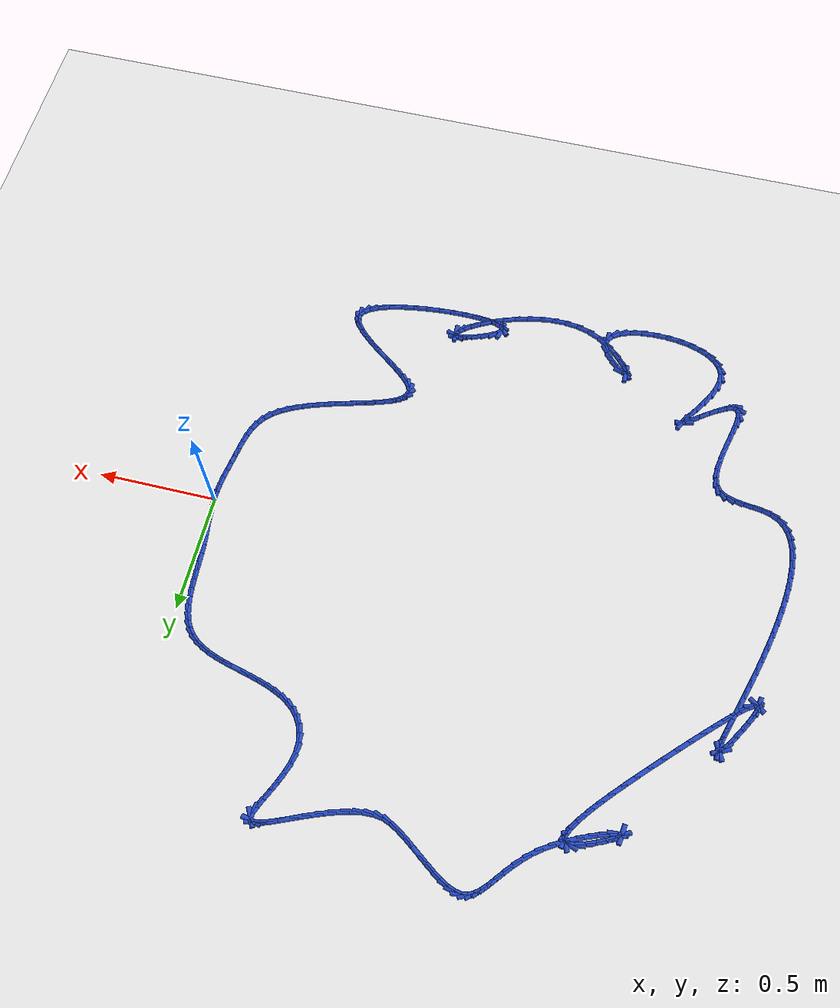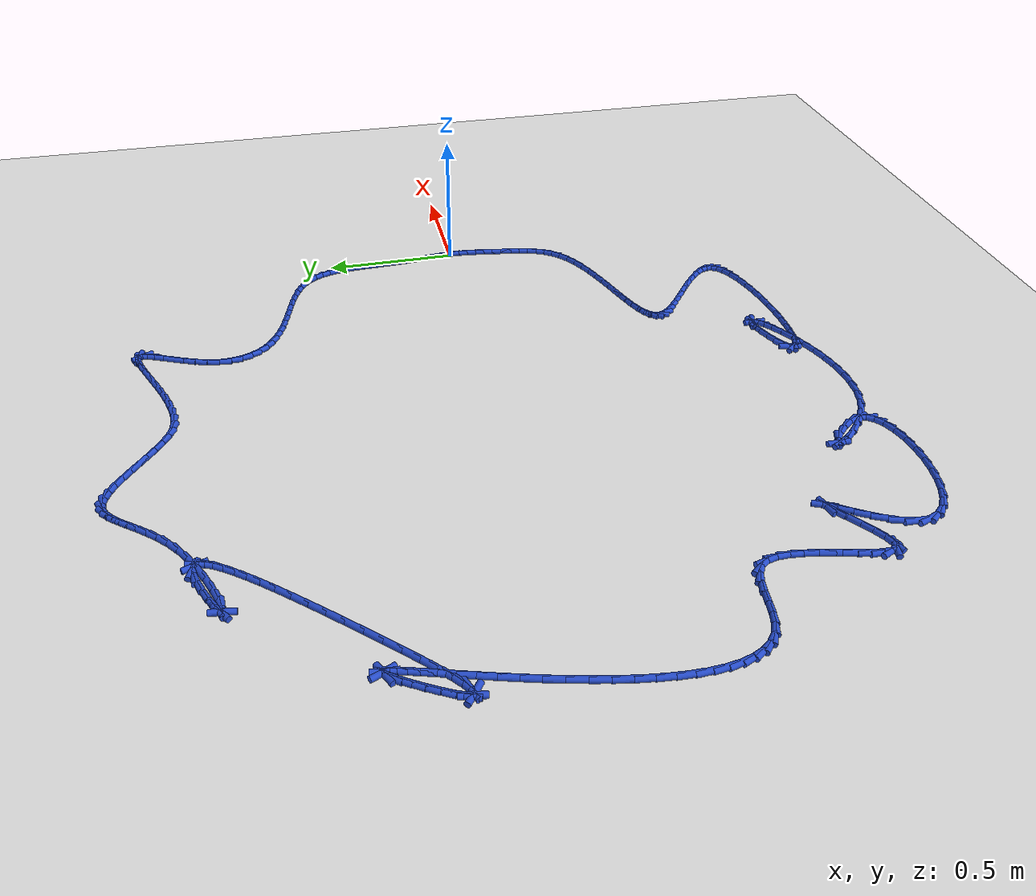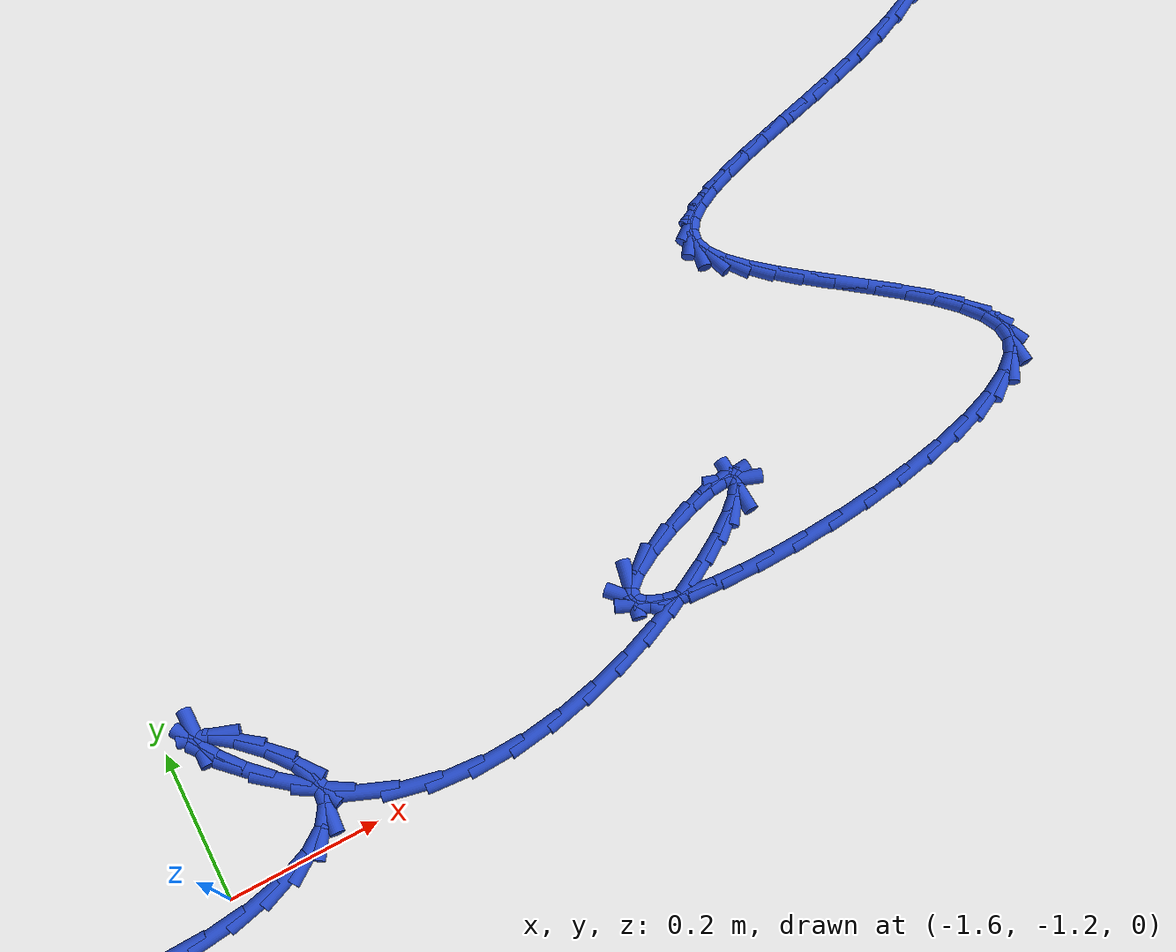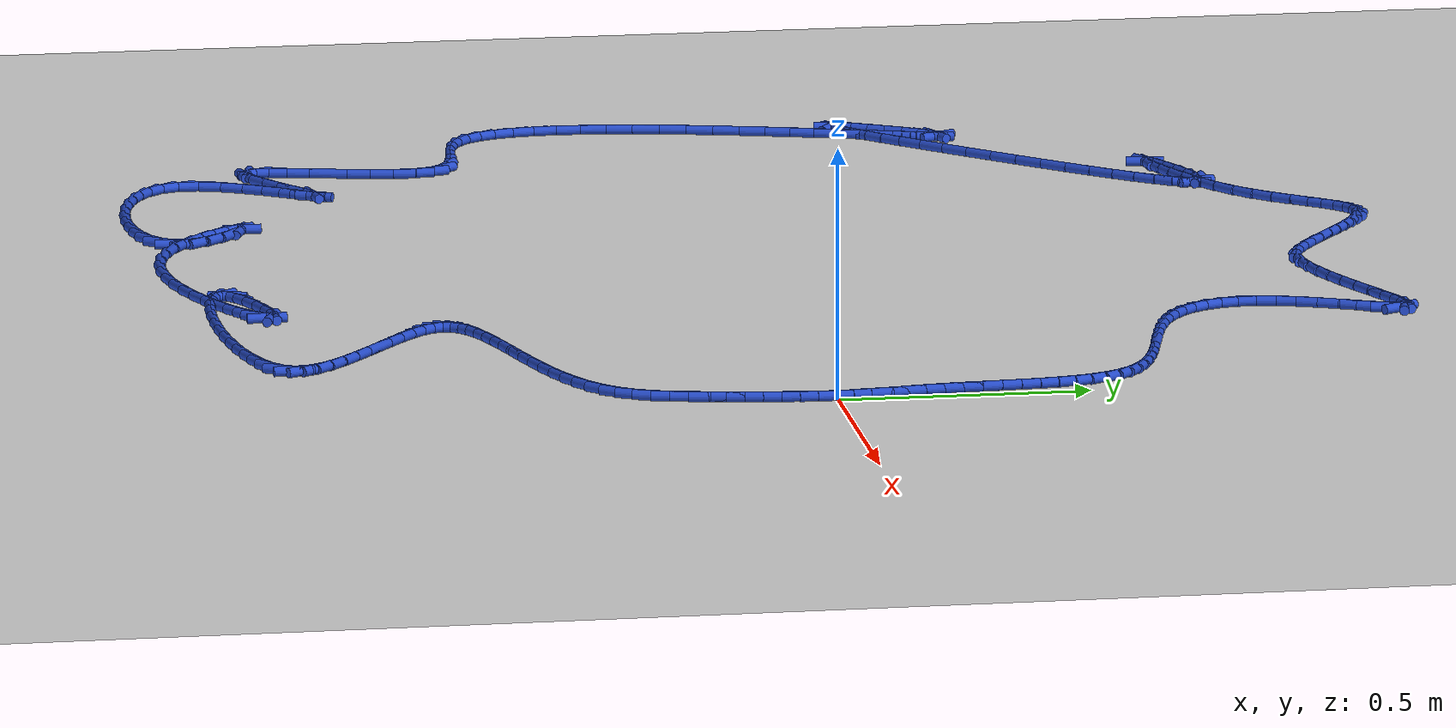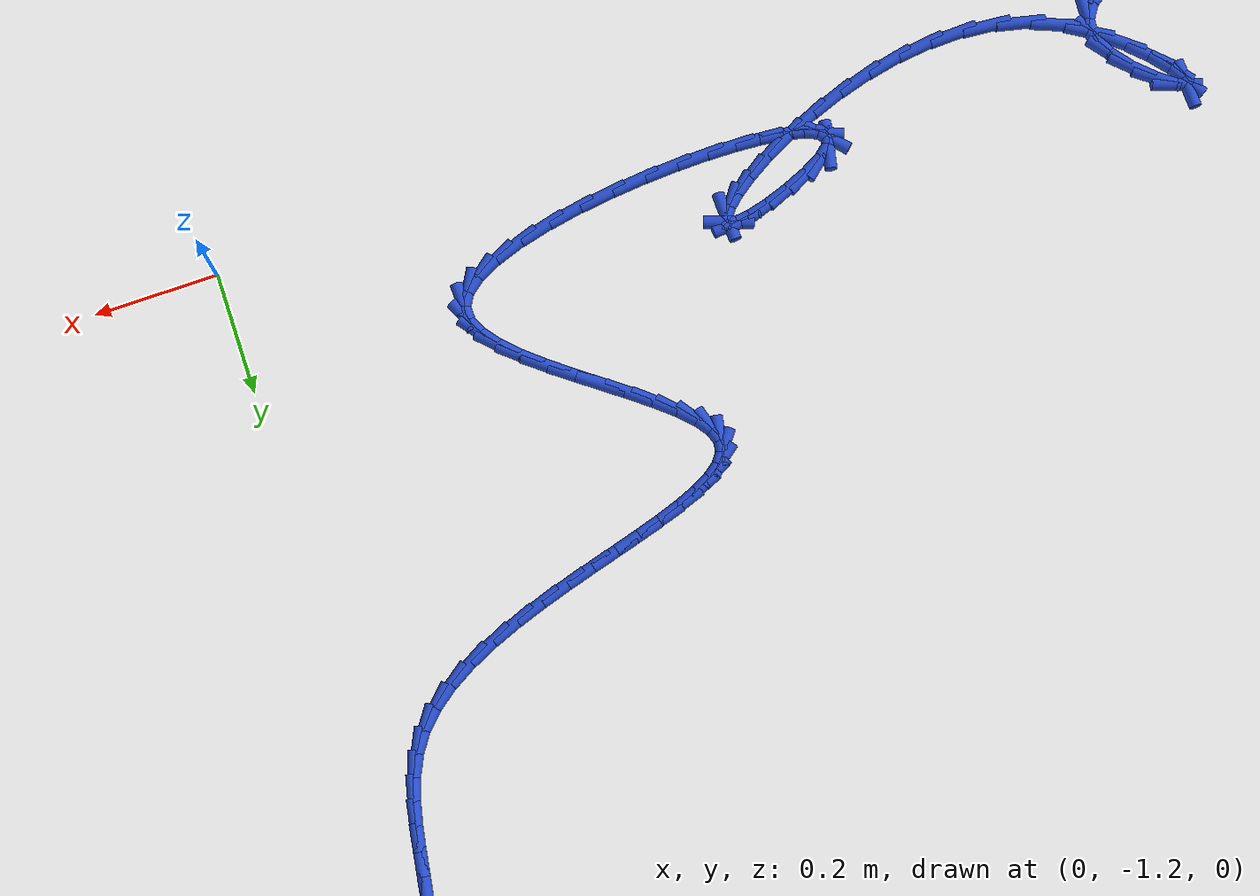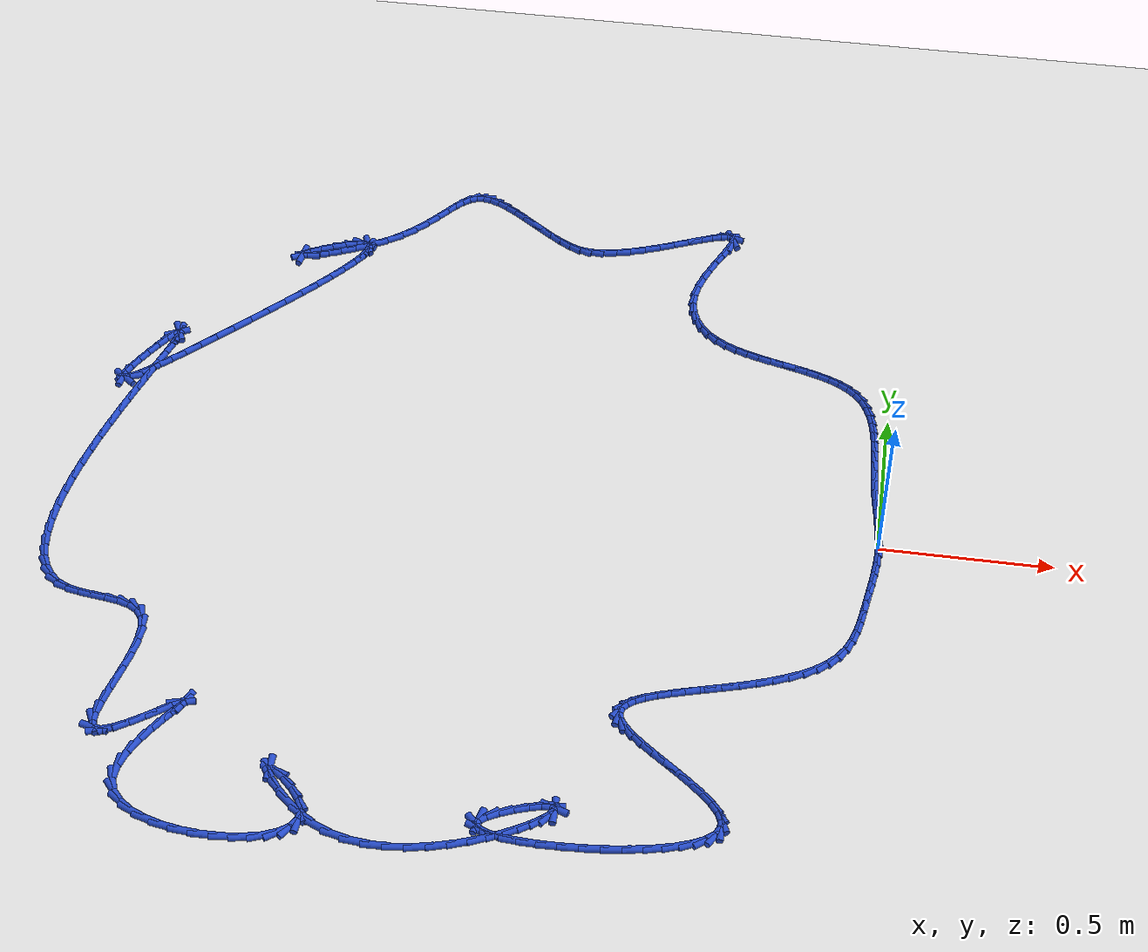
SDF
<sdf version="1.6">
 <world name="default">
  <light name="sun" type="directional">
   <pose>0 0 10 0 -0 0</pose>
   <diffuse>0.8 0.8 0.8 1</diffuse>
   <specular>0.2 0.2 0.2 1</specular>
   <attenuation>
    <range>1000</range>
    <constant>0.9</constant>
    <linear>0.01</linear>
    <quadratic>0.001</quadratic>
   </attenuation>
   <direction>-0.5 0.1 -0.9</direction>
  </light>
  <model name="ground_plane">
   <static>1</static>
   <link name="link">
    <collision name="collision">
     <geometry><plane><normal>0 0 1</normal><size>100 100</size></plane></geometry>
     <surface><friction><ode><mu>100</mu><mu2>50</mu2></ode></friction></surface>
    </collision>
    <visual name="visual">
     <cast_shadows>0</cast_shadows>
     <geometry><plane><normal>0 0 1</normal><size>100 100</size></plane></geometry>
     <material>
      <script><uri>file://media/materials/scripts/gazebo.material</uri><name>Gazebo/WhiteGlow</name></script>
     </material>
    </visual>
   </link>
  </model>
  <gravity>0 0 -9.8</gravity>
  <magnetic_field>6e-06 2.3e-05 -4.2e-05</magnetic_field>
  <atmosphere type="adiabatic"/>
  <physics name="default_physics" default="0" type="ode">
   <max_step_size>0.001</max_step_size>
   <real_time_factor>1</real_time_factor>
   <real_time_update_rate>1000</real_time_update_rate>
  </physics>
  <scene><ambient>0.4 0.4 0.4 1</ambient><background>0.7 0.7 0.7 1</background><shadows>1</shadows></scene>
  <spherical_coordinates>
   <surface_model>EARTH_WGS84</surface_model>
   <latitude_deg>0</latitude_deg>
   <longitude_deg>0</longitude_deg>
   <elevation>0</elevation>
   <heading_deg>0</heading_deg>
  </spherical_coordinates>
  <model name="line">
   <link name="link_0">
    <pose>5.204170427930421e-18 -6.938893903907228e-18 0.01 0 1.57 -1.525466865346189</pose>
    <collision name="collision">
     <geometry><cylinder><radius>0.01</radius><length>0.08</length></cylinder></geometry>
    </collision>
    <visual name="visual">
     <material>
      <script><name>Gazebo/Blue</name><uri>file://media/materials/scripts/gazebo.material</uri></script>
     </material>
     <geometry><cylinder><radius>0.01</radius><length>0.08</length></cylinder></geometry>
    </visual>
   </link>
   <link name="link_1">
    <pose>-0.0015726890717576289 0.03467086763680368 0.01 0 1.57 -1.476173963421705</pose>
    <collision name="collision">
     <geometry><cylinder><radius>0.01</radius><length>0.08</length></cylinder></geometry>
    </collision>
    <visual name="visual">
     <material>
      <script><name>Gazebo/Blue</name><uri>file://media/materials/scripts/gazebo.material</uri></script>
     </material>
     <geometry><cylinder><radius>0.01</radius><length>0.08</length></cylinder></geometry>
    </visual>
   </link>
   <link name="link_2">
    <pose>-0.0048644142566176 0.06935500745359917 0.01 0 1.57 -1.4452423699175796</pose>
    <collision name="collision">
     <geometry><cylinder><radius>0.01</radius><length>0.08</length></cylinder></geometry>
    </collision>
    <visual name="visual">
     <material>
      <script><name>Gazebo/Blue</name><uri>file://media/materials/scripts/gazebo.material</uri></script>
     </material>
     <geometry><cylinder><radius>0.01</radius><length>0.08</length></cylinder></geometry>
    </visual>
   </link>
   <link name="link_3">
    <pose>-0.009272969059401427 0.10428313990101569 0.01 0 1.57 -1.4326208207517068</pose>
    <collision name="collision">
     <geometry><cylinder><radius>0.01</radius><length>0.08</length></cylinder></geometry>
    </collision>
    <visual name="visual">
     <material>
      <script><name>Gazebo/Blue</name><uri>file://media/materials/scripts/gazebo.material</uri></script>
     </material>
     <geometry><cylinder><radius>0.01</radius><length>0.08</length></cylinder></geometry>
    </visual>
   </link>
   <link name="link_4">
    <pose>-0.014196146984930666 0.13968598542968272 0.01 0 1.57 -1.437669131877646</pose>
    <collision name="collision">
     <geometry><cylinder><radius>0.01</radius><length>0.08</length></cylinder></geometry>
    </collision>
    <visual name="visual">
     <material>
      <script><name>Gazebo/Blue</name><uri>file://media/materials/scripts/gazebo.material</uri></script>
     </material>
     <geometry><cylinder><radius>0.01</radius><length>0.08</length></cylinder></geometry>
    </visual>
   </link>
   <link name="link_5">
    <pose>-0.019031741538026826 0.17579426449022945 0.01 0 1.57 -1.4593457047023486</pose>
    <collision name="collision">
     <geometry><cylinder><radius>0.01</radius><length>0.08</length></cylinder></geometry>
    </collision>
    <visual name="visual">
     <material>
      <script><name>Gazebo/Blue</name><uri>file://media/materials/scripts/gazebo.material</uri></script>
     </material>
     <geometry><cylinder><radius>0.01</radius><length>0.08</length></cylinder></geometry>
    </visual>
   </link>
   <link name="link_6">
    <pose>-0.023177546223511463 0.21283869753328535 0.01 0 1.57 -1.4918491704939212</pose>
    <collision name="collision">
     <geometry><cylinder><radius>0.01</radius><length>0.08</length></cylinder></geometry>
    </collision>
    <visual name="visual">
     <material>
      <script><name>Gazebo/Blue</name><uri>file://media/materials/scripts/gazebo.material</uri></script>
     </material>
     <geometry><cylinder><radius>0.01</radius><length>0.08</length></cylinder></geometry>
    </visual>
   </link>
   <link name="link_7">
    <pose>-0.026192747832759933 0.25095197368180616 0.01 0 1.57 -1.5139920718391748</pose>
    <collision name="collision">
     <geometry><cylinder><radius>0.01</radius><length>0.08</length></cylinder></geometry>
    </collision>
    <visual name="visual">
     <material>
      <script><name>Gazebo/Blue</name><uri>file://media/materials/scripts/gazebo.material</uri></script>
     </material>
     <geometry><cylinder><radius>0.01</radius><length>0.08</length></cylinder></geometry>
    </visual>
   </link>
   <link name="link_8">
    <pose>-0.02840196308097421 0.2898018549649636 0.01 0 1.57 -1.520871027531052</pose>
    <collision name="collision">
     <geometry><cylinder><radius>0.01</radius><length>0.08</length></cylinder></geometry>
    </collision>
    <visual name="visual">
     <material>
      <script><name>Gazebo/Blue</name><uri>file://media/materials/scripts/gazebo.material</uri></script>
     </material>
     <geometry><cylinder><radius>0.01</radius><length>0.08</length></cylinder></geometry>
    </visual>
   </link>
   <link name="link_9">
    <pose>-0.030356493168150502 0.3289184137875223 0.01 0 1.57 -1.5130095171058313</pose>
    <collision name="collision">
     <geometry><cylinder><radius>0.01</radius><length>0.08</length></cylinder></geometry>
    </collision>
    <visual name="visual">
     <material>
      <script><name>Gazebo/Blue</name><uri>file://media/materials/scripts/gazebo.material</uri></script>
     </material>
     <geometry><cylinder><radius>0.01</radius><length>0.08</length></cylinder></geometry>
    </visual>
   </link>
   <link name="link_10">
    <pose>-0.03260767426788891 0.36783170131105386 0.01 0 1.57 -1.4899280205731082</pose>
    <collision name="collision">
     <geometry><cylinder><radius>0.01</radius><length>0.08</length></cylinder></geometry>
    </collision>
    <visual name="visual">
     <material>
      <script><name>Gazebo/Blue</name><uri>file://media/materials/scripts/gazebo.material</uri></script>
     </material>
     <geometry><cylinder><radius>0.01</radius><length>0.08</length></cylinder></geometry>
    </visual>
   </link>
   <link name="link_11">
    <pose>-0.0357068425537895 0.4060717686971295 0.01 0 1.57 -1.4501222387260886</pose>
    <collision name="collision">
     <geometry><cylinder><radius>0.01</radius><length>0.08</length></cylinder></geometry>
    </collision>
    <visual name="visual">
     <material>
      <script><name>Gazebo/Blue</name><uri>file://media/materials/scripts/gazebo.material</uri></script>
     </material>
     <geometry><cylinder><radius>0.01</radius><length>0.08</length></cylinder></geometry>
    </visual>
   </link>
   <link name="link_12">
    <pose>-0.0402053341994524 0.44316866710732067 0.01 0 1.57 -1.3910095355730463</pose>
    <collision name="collision">
     <geometry><cylinder><radius>0.01</radius><length>0.08</length></cylinder></geometry>
    </collision>
    <visual name="visual">
     <material>
      <script><name>Gazebo/Blue</name><uri>file://media/materials/scripts/gazebo.material</uri></script>
     </material>
     <geometry><cylinder><radius>0.01</radius><length>0.08</length></cylinder></geometry>
    </visual>
   </link>
   <link name="link_13">
    <pose>-0.046654485378477654 0.4786524477031986 0.01 0 1.57 -1.3089563637968882</pose>
    <collision name="collision">
     <geometry><cylinder><radius>0.01</radius><length>0.08</length></cylinder></geometry>
    </collision>
    <visual name="visual">
     <material>
      <script><name>Gazebo/Blue</name><uri>file://media/materials/scripts/gazebo.material</uri></script>
     </material>
     <geometry><cylinder><radius>0.01</radius><length>0.08</length></cylinder></geometry>
    </visual>
   </link>
   <link name="link_14">
    <pose>-0.055605632264465396 0.5120531616463349 0.01 0 1.57 -1.1996755198462907</pose>
    <collision name="collision">
     <geometry><cylinder><radius>0.01</radius><length>0.08</length></cylinder></geometry>
    </collision>
    <visual name="visual">
     <material>
      <script><name>Gazebo/Blue</name><uri>file://media/materials/scripts/gazebo.material</uri></script>
     </material>
     <geometry><cylinder><radius>0.01</radius><length>0.08</length></cylinder></geometry>
    </visual>
   </link>
   <link name="link_15">
    <pose>-0.06761011103101566 0.5429008600983004 0.01 0 1.57 -1.0595615241486003</pose>
    <collision name="collision">
     <geometry><cylinder><radius>0.01</radius><length>0.08</length></cylinder></geometry>
    </collision>
    <visual name="visual">
     <material>
      <script><name>Gazebo/Blue</name><uri>file://media/materials/scripts/gazebo.material</uri></script>
     </material>
     <geometry><cylinder><radius>0.01</radius><length>0.08</length></cylinder></geometry>
    </visual>
   </link>
   <link name="link_16">
    <pose>-0.08321925785172851 0.5707255942206667 0.01 0 1.57 -0.8887410565504138</pose>
    <collision name="collision">
     <geometry><cylinder><radius>0.01</radius><length>0.08</length></cylinder></geometry>
    </collision>
    <visual name="visual">
     <material>
      <script><name>Gazebo/Blue</name><uri>file://media/materials/scripts/gazebo.material</uri></script>
     </material>
     <geometry><cylinder><radius>0.01</radius><length>0.08</length></cylinder></geometry>
    </visual>
   </link>
   <link name="link_17">
    <pose>-0.10298084332388467 0.5950605346263621 0.01 0 1.57 -0.7100038560354098</pose>
    <collision name="collision">
     <geometry><cylinder><radius>0.01</radius><length>0.08</length></cylinder></geometry>
    </collision>
    <visual name="visual">
     <material>
      <script><name>Gazebo/Blue</name><uri>file://media/materials/scripts/gazebo.material</uri></script>
     </material>
     <geometry><cylinder><radius>0.01</radius><length>0.08</length></cylinder></geometry>
    </visual>
   </link>
   <link name="link_18">
    <pose>-0.1270693361858647 0.6157654462529885 0.01 0 1.57 -0.5614147246949308</pose>
    <collision name="collision">
     <geometry><cylinder><radius>0.01</radius><length>0.08</length></cylinder></geometry>
    </collision>
    <visual name="visual">
     <material>
      <script><name>Gazebo/Blue</name><uri>file://media/materials/scripts/gazebo.material</uri></script>
     </material>
     <geometry><cylinder><radius>0.01</radius><length>0.08</length></cylinder></geometry>
    </visual>
   </link>
   <link name="link_19">
    <pose>-0.1549635335831919 0.6333087231907982 0.01 0 1.57 -0.4471855887108201</pose>
    <collision name="collision">
     <geometry><cylinder><radius>0.01</radius><length>0.08</length></cylinder></geometry>
    </collision>
    <visual name="visual">
     <material>
      <script><name>Gazebo/Blue</name><uri>file://media/materials/scripts/gazebo.material</uri></script>
     </material>
     <geometry><cylinder><radius>0.01</radius><length>0.08</length></cylinder></geometry>
    </visual>
   </link>
   <link name="link_20">
    <pose>-0.18606625197703033 0.648225233510027 0.01 0 1.57 -0.3634909186812425</pose>
    <collision name="collision">
     <geometry><cylinder><radius>0.01</radius><length>0.08</length></cylinder></geometry>
    </collision>
    <visual name="visual">
     <material>
      <script><name>Gazebo/Blue</name><uri>file://media/materials/scripts/gazebo.material</uri></script>
     </material>
     <geometry><cylinder><radius>0.01</radius><length>0.08</length></cylinder></geometry>
    </visual>
   </link>
   <link name="link_21">
    <pose>-0.21978030782854388 0.6610498452809117 0.01 0 1.57 -0.30549677306807743</pose>
    <collision name="collision">
     <geometry><cylinder><radius>0.01</radius><length>0.08</length></cylinder></geometry>
    </collision>
    <visual name="visual">
     <material>
      <script><name>Gazebo/Blue</name><uri>file://media/materials/scripts/gazebo.material</uri></script>
     </material>
     <geometry><cylinder><radius>0.01</radius><length>0.08</length></cylinder></geometry>
    </visual>
   </link>
   <link name="link_22">
    <pose>-0.25550851759889637 0.6723174265736881 0.01 0 1.57 -0.2691292814759106</pose>
    <collision name="collision">
     <geometry><cylinder><radius>0.01</radius><length>0.08</length></cylinder></geometry>
    </collision>
    <visual name="visual">
     <material>
      <script><name>Gazebo/Blue</name><uri>file://media/materials/scripts/gazebo.material</uri></script>
     </material>
     <geometry><cylinder><radius>0.01</radius><length>0.08</length></cylinder></geometry>
    </visual>
   </link>
   <link name="link_23">
    <pose>-0.29265369774925176 0.6825628454585926 0.01 0 1.57 -0.2515838415232816</pose>
    <collision name="collision">
     <geometry><cylinder><radius>0.01</radius><length>0.08</length></cylinder></geometry>
    </collision>
    <visual name="visual">
     <material>
      <script><name>Gazebo/Blue</name><uri>file://media/materials/scripts/gazebo.material</uri></script>
     </material>
     <geometry><cylinder><radius>0.01</radius><length>0.08</length></cylinder></geometry>
    </visual>
   </link>
   <link name="link_24">
    <pose>-0.33061866474077434 0.6923209700058615 0.01 0 1.57 -0.25134698519280896</pose>
    <collision name="collision">
     <geometry><cylinder><radius>0.01</radius><length>0.08</length></cylinder></geometry>
    </collision>
    <visual name="visual">
     <material>
      <script><name>Gazebo/Blue</name><uri>file://media/materials/scripts/gazebo.material</uri></script>
     </material>
     <geometry><cylinder><radius>0.01</radius><length>0.08</length></cylinder></geometry>
    </visual>
   </link>
   <link name="link_25">
    <pose>-0.36880623503462784 0.7021266682857306 0.01 0 1.57 -0.2681097011331625</pose>
    <collision name="collision">
     <geometry><cylinder><radius>0.01</radius><length>0.08</length></cylinder></geometry>
    </collision>
    <visual name="visual">
     <material>
      <script><name>Gazebo/Blue</name><uri>file://media/materials/scripts/gazebo.material</uri></script>
     </material>
     <geometry><cylinder><radius>0.01</radius><length>0.08</length></cylinder></geometry>
    </visual>
   </link>
   <link name="link_26">
    <pose>-0.40661922509197596 0.7125148083684368 0.01 0 1.57 -0.3027010437539615</pose>
    <collision name="collision">
     <geometry><cylinder><radius>0.01</radius><length>0.08</length></cylinder></geometry>
    </collision>
    <visual name="visual">
     <material>
      <script><name>Gazebo/Blue</name><uri>file://media/materials/scripts/gazebo.material</uri></script>
     </material>
     <geometry><cylinder><radius>0.01</radius><length>0.08</length></cylinder></geometry>
    </visual>
   </link>
   <link name="link_27">
    <pose>-0.4434604513739828 0.7240202583242159 0.01 0 1.57 -0.3570426701770385</pose>
    <collision name="collision">
     <geometry><cylinder><radius>0.01</radius><length>0.08</length></cylinder></geometry>
    </collision>
    <visual name="visual">
     <material>
      <script><name>Gazebo/Blue</name><uri>file://media/materials/scripts/gazebo.material</uri></script>
     </material>
     <geometry><cylinder><radius>0.01</radius><length>0.08</length></cylinder></geometry>
    </visual>
   </link>
   <link name="link_28">
    <pose>-0.47873273034181263 0.7371778862233043 0.01 0 1.57 -0.4340230013759574</pose>
    <collision name="collision">
     <geometry><cylinder><radius>0.01</radius><length>0.08</length></cylinder></geometry>
    </collision>
    <visual name="visual">
     <material>
      <script><name>Gazebo/Blue</name><uri>file://media/materials/scripts/gazebo.material</uri></script>
     </material>
     <geometry><cylinder><radius>0.01</radius><length>0.08</length></cylinder></geometry>
    </visual>
   </link>
   <link name="link_29">
    <pose>-0.5118388784566292 0.7525225601359382 0.01 0 1.57 -0.537041591197063</pose>
    <collision name="collision">
     <geometry><cylinder><radius>0.01</radius><length>0.08</length></cylinder></geometry>
    </collision>
    <visual name="visual">
     <material>
      <script><name>Gazebo/Blue</name><uri>file://media/materials/scripts/gazebo.material</uri></script>
     </material>
     <geometry><cylinder><radius>0.01</radius><length>0.08</length></cylinder></geometry>
    </visual>
   </link>
   <link name="link_30">
    <pose>-0.5421817121795963 0.7705891481323538 0.01 0 1.57 -0.6687806964344242</pose>
    <collision name="collision">
     <geometry><cylinder><radius>0.01</radius><length>0.08</length></cylinder></geometry>
    </collision>
    <visual name="visual">
     <material>
      <script><name>Gazebo/Blue</name><uri>file://media/materials/scripts/gazebo.material</uri></script>
     </material>
     <geometry><cylinder><radius>0.01</radius><length>0.08</length></cylinder></geometry>
    </visual>
   </link>
   <link name="link_31">
    <pose>-0.5691640479718779 0.7919125182827872 0.01 0 1.57 -0.8287938160876648</pose>
    <collision name="collision">
     <geometry><cylinder><radius>0.01</radius><length>0.08</length></cylinder></geometry>
    </collision>
    <visual name="visual">
     <material>
      <script><name>Gazebo/Blue</name><uri>file://media/materials/scripts/gazebo.material</uri></script>
     </material>
     <geometry><cylinder><radius>0.01</radius><length>0.08</length></cylinder></geometry>
    </visual>
   </link>
   <link name="link_32">
    <pose>-0.5921887021559505 0.8170275373524093 0.01 0 1.57 -1.008055546454614</pose>
    <collision name="collision">
     <geometry><cylinder><radius>0.01</radius><length>0.08</length></cylinder></geometry>
    </collision>
    <visual name="visual">
     <material>
      <script><name>Gazebo/Blue</name><uri>file://media/materials/scripts/gazebo.material</uri></script>
     </material>
     <geometry><cylinder><radius>0.01</radius><length>0.08</length></cylinder></geometry>
    </visual>
   </link>
   <link name="link_33">
    <pose>-0.6106379929205288 0.8462761823557295 0.01 0 1.57 -1.190800888467741</pose>
    <collision name="collision">
     <geometry><cylinder><radius>0.01</radius><length>0.08</length></cylinder></geometry>
    </collision>
    <visual name="visual">
     <material>
      <script><name>Gazebo/Blue</name><uri>file://media/materials/scripts/gazebo.material</uri></script>
     </material>
     <geometry><cylinder><radius>0.01</radius><length>0.08</length></cylinder></geometry>
    </visual>
   </link>
   <link name="link_34">
    <pose>-0.6238168514182505 0.8792722095693919 0.01 0 1.57 -1.3745162825788582</pose>
    <collision name="collision">
     <geometry><cylinder><radius>0.01</radius><length>0.08</length></cylinder></geometry>
    </collision>
    <visual name="visual">
     <material>
      <script><name>Gazebo/Blue</name><uri>file://media/materials/scripts/gazebo.material</uri></script>
     </material>
     <geometry><cylinder><radius>0.01</radius><length>0.08</length></cylinder></geometry>
    </visual>
   </link>
   <link name="link_35">
    <pose>-0.6310119494336793 0.9154575525569977 0.01 0 1.57 -1.5579672254800017</pose>
    <collision name="collision">
     <geometry><cylinder><radius>0.01</radius><length>0.08</length></cylinder></geometry>
    </collision>
    <visual name="visual">
     <material>
      <script><name>Gazebo/Blue</name><uri>file://media/materials/scripts/gazebo.material</uri></script>
     </material>
     <geometry><cylinder><radius>0.01</radius><length>0.08</length></cylinder></geometry>
    </visual>
   </link>
   <link name="link_36">
    <pose>-0.6315099587513782 0.9542741448821481 0.01 0 1.57 1.411901880810581</pose>
    <collision name="collision">
     <geometry><cylinder><radius>0.01</radius><length>0.08</length></cylinder></geometry>
    </collision>
    <visual name="visual">
     <material>
      <script><name>Gazebo/Blue</name><uri>file://media/materials/scripts/gazebo.material</uri></script>
     </material>
     <geometry><cylinder><radius>0.01</radius><length>0.08</length></cylinder></geometry>
    </visual>
   </link>
   <link name="link_37">
    <pose>-0.6249741604738228 0.9950603496126849 0.01 0 1.57 1.2879114870810962</pose>
    <collision name="collision">
     <geometry><cylinder><radius>0.01</radius><length>0.08</length></cylinder></geometry>
    </collision>
    <visual name="visual">
     <material>
      <script><name>Gazebo/Blue</name><uri>file://media/materials/scripts/gazebo.material</uri></script>
     </material>
     <geometry><cylinder><radius>0.01</radius><length>0.08</length></cylinder></geometry>
    </visual>
   </link>
   <link name="link_38">
    <pose>-0.6128833415887832 1.0366552515573897 0.01 0 1.57 1.207531063588702</pose>
    <collision name="collision">
     <geometry><cylinder><radius>0.01</radius><length>0.08</length></cylinder></geometry>
    </collision>
    <visual name="visual">
     <material>
      <script><name>Gazebo/Blue</name><uri>file://media/materials/scripts/gazebo.material</uri></script>
     </material>
     <geometry><cylinder><radius>0.01</radius><length>0.08</length></cylinder></geometry>
    </visual>
   </link>
   <link name="link_39">
    <pose>-0.5972626575549644 1.0777476799399857 0.01 0 1.57 1.1596509893311557</pose>
    <collision name="collision">
     <geometry><cylinder><radius>0.01</radius><length>0.08</length></cylinder></geometry>
    </collision>
    <visual name="visual">
     <material>
      <script><name>Gazebo/Blue</name><uri>file://media/materials/scripts/gazebo.material</uri></script>
     </material>
     <geometry><cylinder><radius>0.01</radius><length>0.08</length></cylinder></geometry>
    </visual>
   </link>
   <link name="link_40">
    <pose>-0.5801373729669529 1.117026433970977 0.01 0 1.57 1.1402550407716003</pose>
    <collision name="collision">
     <geometry><cylinder><radius>0.01</radius><length>0.08</length></cylinder></geometry>
    </collision>
    <visual name="visual">
     <material>
      <script><name>Gazebo/Blue</name><uri>file://media/materials/scripts/gazebo.material</uri></script>
     </material>
     <geometry><cylinder><radius>0.01</radius><length>0.08</length></cylinder></geometry>
    </visual>
   </link>
   <link name="link_41">
    <pose>-0.5635327524193348 1.1531803128608682 0.01 0 1.57 1.1535757710899832</pose>
    <collision name="collision">
     <geometry><cylinder><radius>0.01</radius><length>0.08</length></cylinder></geometry>
    </collision>
    <visual name="visual">
     <material>
      <script><name>Gazebo/Blue</name><uri>file://media/materials/scripts/gazebo.material</uri></script>
     </material>
     <geometry><cylinder><radius>0.01</radius><length>0.08</length></cylinder></geometry>
    </visual>
   </link>
   <link name="link_42">
    <pose>-0.5494740605066963 1.1848981158201646 0.01 0 1.57 1.2205409538286702</pose>
    <collision name="collision">
     <geometry><cylinder><radius>0.01</radius><length>0.08</length></cylinder></geometry>
    </collision>
    <visual name="visual">
     <material>
      <script><name>Gazebo/Blue</name><uri>file://media/materials/scripts/gazebo.material</uri></script>
     </material>
     <geometry><cylinder><radius>0.01</radius><length>0.08</length></cylinder></geometry>
    </visual>
   </link>
   <link name="link_43">
    <pose>-0.5399865618236241 1.2108686420593706 0.01 0 1.57 1.4191029968428943</pose>
    <collision name="collision">
     <geometry><cylinder><radius>0.01</radius><length>0.08</length></cylinder></geometry>
    </collision>
    <visual name="visual">
     <material>
      <script><name>Gazebo/Blue</name><uri>file://media/materials/scripts/gazebo.material</uri></script>
     </material>
     <geometry><cylinder><radius>0.01</radius><length>0.08</length></cylinder></geometry>
    </visual>
   </link>
   <link name="link_44">
    <pose>-0.5370955209647044 1.229780690788992 0.01 0 1.57 -1.0968200849039615</pose>
    <collision name="collision">
     <geometry><cylinder><radius>0.01</radius><length>0.08</length></cylinder></geometry>
    </collision>
    <visual name="visual">
     <material>
      <script><name>Gazebo/Blue</name><uri>file://media/materials/scripts/gazebo.material</uri></script>
     </material>
     <geometry><cylinder><radius>0.01</radius><length>0.08</length></cylinder></geometry>
    </visual>
   </link>
   <link name="link_45">
    <pose>-0.5426006619674212 1.2405124142446236 0.01 0 1.57 -0.2127903457579623</pose>
    <collision name="collision">
     <geometry><cylinder><radius>0.01</radius><length>0.08</length></cylinder></geometry>
    </collision>
    <visual name="visual">
     <material>
      <script><name>Gazebo/Blue</name><uri>file://media/materials/scripts/gazebo.material</uri></script>
     </material>
     <geometry><cylinder><radius>0.01</radius><length>0.08</length></cylinder></geometry>
    </visual>
   </link>
   <link name="link_46">
    <pose>-0.5564422796925125 1.2435030521402366 0.01 0 1.57 0.16556101545826774</pose>
    <collision name="collision">
     <geometry><cylinder><radius>0.01</radius><length>0.08</length></cylinder></geometry>
    </collision>
    <visual name="visual">
     <material>
      <script><name>Gazebo/Blue</name><uri>file://media/materials/scripts/gazebo.material</uri></script>
     </material>
     <geometry><cylinder><radius>0.01</radius><length>0.08</length></cylinder></geometry>
    </visual>
   </link>
   <link name="link_47">
    <pose>-0.5776454709031361 1.2399602005801604 0.01 0 1.57 0.3109083794844831</pose>
    <collision name="collision">
     <geometry><cylinder><radius>0.01</radius><length>0.08</length></cylinder></geometry>
    </collision>
    <visual name="visual">
     <material>
      <script><name>Gazebo/Blue</name><uri>file://media/materials/scripts/gazebo.material</uri></script>
     </material>
     <geometry><cylinder><radius>0.01</radius><length>0.08</length></cylinder></geometry>
    </visual>
   </link>
   <link name="link_48">
    <pose>-0.6052289418680638 1.231096820821046 0.01 0 1.57 0.3746895385349172</pose>
    <collision name="collision">
     <geometry><cylinder><radius>0.01</radius><length>0.08</length></cylinder></geometry>
    </collision>
    <visual name="visual">
     <material>
      <script><name>Gazebo/Blue</name><uri>file://media/materials/scripts/gazebo.material</uri></script>
     </material>
     <geometry><cylinder><radius>0.01</radius><length>0.08</length></cylinder></geometry>
    </visual>
   </link>
   <link name="link_49">
    <pose>-0.6382113988560678 1.2181258741195429 0.01 0 1.57 0.40120211457559063</pose>
    <collision name="collision">
     <geometry><cylinder><radius>0.01</radius><length>0.08</length></cylinder></geometry>
    </collision>
    <visual name="visual">
     <material>
      <script><name>Gazebo/Blue</name><uri>file://media/materials/scripts/gazebo.material</uri></script>
     </material>
     <geometry><cylinder><radius>0.01</radius><length>0.08</length></cylinder></geometry>
    </visual>
   </link>
   <link name="link_50">
    <pose>-0.6756115481359201 1.2022603217323025 0.01 0 1.57 0.4058393092878728</pose>
    <collision name="collision">
     <geometry><cylinder><radius>0.01</radius><length>0.08</length></cylinder></geometry>
    </collision>
    <visual name="visual">
     <material>
      <script><name>Gazebo/Blue</name><uri>file://media/materials/scripts/gazebo.material</uri></script>
     </material>
     <geometry><cylinder><radius>0.01</radius><length>0.08</length></cylinder></geometry>
    </visual>
   </link>
   <link name="link_51">
    <pose>-0.7164480959763923 1.1847131249159755 0.01 0 1.57 0.39435195863110273</pose>
    <collision name="collision">
     <geometry><cylinder><radius>0.01</radius><length>0.08</length></cylinder></geometry>
    </collision>
    <visual name="visual">
     <material>
      <script><name>Gazebo/Blue</name><uri>file://media/materials/scripts/gazebo.material</uri></script>
     </material>
     <geometry><cylinder><radius>0.01</radius><length>0.08</length></cylinder></geometry>
    </visual>
   </link>
   <link name="link_52">
    <pose>-0.7597397486462572 1.1666972449272117 0.01 0 1.57 0.36822649900544446</pose>
    <collision name="collision">
     <geometry><cylinder><radius>0.01</radius><length>0.08</length></cylinder></geometry>
    </collision>
    <visual name="visual">
     <material>
      <script><name>Gazebo/Blue</name><uri>file://media/materials/scripts/gazebo.material</uri></script>
     </material>
     <geometry><cylinder><radius>0.01</radius><length>0.08</length></cylinder></geometry>
    </visual>
   </link>
   <link name="link_53">
    <pose>-0.8045052124142866 1.1494256430226621 0.01 0 1.57 0.3262850010313419</pose>
    <collision name="collision">
     <geometry><cylinder><radius>0.01</radius><length>0.08</length></cylinder></geometry>
    </collision>
    <visual name="visual">
     <material>
      <script><name>Gazebo/Blue</name><uri>file://media/materials/scripts/gazebo.material</uri></script>
     </material>
     <geometry><cylinder><radius>0.01</radius><length>0.08</length></cylinder></geometry>
    </visual>
   </link>
   <link name="link_54">
    <pose>-0.8497631935492521 1.134111280458978 0.01 0 1.57 0.26488725281545655</pose>
    <collision name="collision">
     <geometry><cylinder><radius>0.01</radius><length>0.08</length></cylinder></geometry>
    </collision>
    <visual name="visual">
     <material>
      <script><name>Gazebo/Blue</name><uri>file://media/materials/scripts/gazebo.material</uri></script>
     </material>
     <geometry><cylinder><radius>0.01</radius><length>0.08</length></cylinder></geometry>
    </visual>
   </link>
   <link name="link_55">
    <pose>-0.8945323983199267 1.121967118492809 0.01 0 1.57 0.17735810649386793</pose>
    <collision name="collision">
     <geometry><cylinder><radius>0.01</radius><length>0.08</length></cylinder></geometry>
    </collision>
    <visual name="visual">
     <material>
      <script><name>Gazebo/Blue</name><uri>file://media/materials/scripts/gazebo.material</uri></script>
     </material>
     <geometry><cylinder><radius>0.01</radius><length>0.08</length></cylinder></geometry>
    </visual>
   </link>
   <link name="link_56">
    <pose>-0.9378315329950817 1.1142061183808063 0.01 0 1.57 0.05294911868341523</pose>
    <collision name="collision">
     <geometry><cylinder><radius>0.01</radius><length>0.08</length></cylinder></geometry>
    </collision>
    <visual name="visual">
     <material>
      <script><name>Gazebo/Blue</name><uri>file://media/materials/scripts/gazebo.material</uri></script>
     </material>
     <geometry><cylinder><radius>0.01</radius><length>0.08</length></cylinder></geometry>
    </visual>
   </link>
   <link name="link_57">
    <pose>-0.9786793038434896 1.1120412413796203 0.01 0 1.57 -0.12349484881316836</pose>
    <collision name="collision">
     <geometry><cylinder><radius>0.01</radius><length>0.08</length></cylinder></geometry>
    </collision>
    <visual name="visual">
     <material>
      <script><name>Gazebo/Blue</name><uri>file://media/materials/scripts/gazebo.material</uri></script>
     </material>
     <geometry><cylinder><radius>0.01</radius><length>0.08</length></cylinder></geometry>
    </visual>
   </link>
   <link name="link_58">
    <pose>-1.0160944171339226 1.116685448745902 0.01 0 1.57 -0.3530125301924481</pose>
    <collision name="collision">
     <geometry><cylinder><radius>0.01</radius><length>0.08</length></cylinder></geometry>
    </collision>
    <visual name="visual">
     <material>
      <script><name>Gazebo/Blue</name><uri>file://media/materials/scripts/gazebo.material</uri></script>
     </material>
     <geometry><cylinder><radius>0.01</radius><length>0.08</length></cylinder></geometry>
    </visual>
   </link>
   <link name="link_59">
    <pose>-1.0495161107083162 1.128999544763535 0.01 0 1.57 -0.5089908944474065</pose>
    <collision name="collision">
     <geometry><cylinder><radius>0.01</radius><length>0.08</length></cylinder></geometry>
    </collision>
    <visual name="visual">
     <material>
      <script><name>Gazebo/Blue</name><uri>file://media/materials/scripts/gazebo.material</uri></script>
     </material>
     <geometry><cylinder><radius>0.01</radius><length>0.08</length></cylinder></geometry>
    </visual>
   </link>
   <link name="link_60">
    <pose>-1.0817292713813056 1.1469756038284262 0.01 0 1.57 -0.5780245154650143</pose>
    <collision name="collision">
     <geometry><cylinder><radius>0.01</radius><length>0.08</length></cylinder></geometry>
    </collision>
    <visual name="visual">
     <material>
      <script><name>Gazebo/Blue</name><uri>file://media/materials/scripts/gazebo.material</uri></script>
     </material>
     <geometry><cylinder><radius>0.01</radius><length>0.08</length></cylinder></geometry>
    </visual>
   </link>
   <link name="link_61">
    <pose>-1.114557933021384 1.168391336665698 0.01 0 1.57 -0.6184746304593443</pose>
    <collision name="collision">
     <geometry><cylinder><radius>0.01</radius><length>0.08</length></cylinder></geometry>
    </collision>
    <visual name="visual">
     <material>
      <script><name>Gazebo/Blue</name><uri>file://media/materials/scripts/gazebo.material</uri></script>
     </material>
     <geometry><cylinder><radius>0.01</radius><length>0.08</length></cylinder></geometry>
    </visual>
   </link>
   <link name="link_62">
    <pose>-1.1477237926727404 1.1919924513080438 0.01 0 1.57 -0.6373206061441989</pose>
    <collision name="collision">
     <geometry><cylinder><radius>0.01</radius><length>0.08</length></cylinder></geometry>
    </collision>
    <visual name="visual">
     <material>
      <script><name>Gazebo/Blue</name><uri>file://media/materials/scripts/gazebo.material</uri></script>
     </material>
     <geometry><cylinder><radius>0.01</radius><length>0.08</length></cylinder></geometry>
    </visual>
   </link>
   <link name="link_63">
    <pose>-1.1808928717030829 1.216550419499615 0.01 0 1.57 -0.6367935510681966</pose>
    <collision name="collision">
     <geometry><cylinder><radius>0.01</radius><length>0.08</length></cylinder></geometry>
    </collision>
    <visual name="visual">
     <material>
      <script><name>Gazebo/Blue</name><uri>file://media/materials/scripts/gazebo.material</uri></script>
     </material>
     <geometry><cylinder><radius>0.01</radius><length>0.08</length></cylinder></geometry>
    </visual>
   </link>
   <link name="link_64">
    <pose>-1.2137311914801197 1.2408367129845632 0.01 0 1.57 -0.6162238736106495</pose>
    <collision name="collision">
     <geometry><cylinder><radius>0.01</radius><length>0.08</length></cylinder></geometry>
    </collision>
    <visual name="visual">
     <material>
      <script><name>Gazebo/Blue</name><uri>file://media/materials/scripts/gazebo.material</uri></script>
     </material>
     <geometry><cylinder><radius>0.01</radius><length>0.08</length></cylinder></geometry>
    </visual>
   </link>
   <link name="link_65">
    <pose>-1.2459047733715571 1.263622803507038 0.01 0 1.57 -0.5717090440675521</pose>
    <collision name="collision">
     <geometry><cylinder><radius>0.01</radius><length>0.08</length></cylinder></geometry>
    </collision>
    <visual name="visual">
     <material>
      <script><name>Gazebo/Blue</name><uri>file://media/materials/scripts/gazebo.material</uri></script>
     </material>
     <geometry><cylinder><radius>0.01</radius><length>0.08</length></cylinder></geometry>
    </visual>
   </link>
   <link name="link_66">
    <pose>-1.2770796387451038 1.2836801628111918 0.01 0 1.57 -0.4947525284520675</pose>
    <collision name="collision">
     <geometry><cylinder><radius>0.01</radius><length>0.08</length></cylinder></geometry>
    </collision>
    <visual name="visual">
     <material>
      <script><name>Gazebo/Blue</name><uri>file://media/materials/scripts/gazebo.material</uri></script>
     </material>
     <geometry><cylinder><radius>0.01</radius><length>0.08</length></cylinder></geometry>
    </visual>
   </link>
   <link name="link_67">
    <pose>-1.3069218089684667 1.2997802626411745 0.01 0 1.57 -0.3695703312416977</pose>
    <collision name="collision">
     <geometry><cylinder><radius>0.01</radius><length>0.08</length></cylinder></geometry>
    </collision>
    <visual name="visual">
     <material>
      <script><name>Gazebo/Blue</name><uri>file://media/materials/scripts/gazebo.material</uri></script>
     </material>
     <geometry><cylinder><radius>0.01</radius><length>0.08</length></cylinder></geometry>
    </visual>
   </link>
   <link name="link_68">
    <pose>-1.3350973054093536 1.3106945747411376 0.01 0 1.57 -0.1702562619580545</pose>
    <collision name="collision">
     <geometry><cylinder><radius>0.01</radius><length>0.08</length></cylinder></geometry>
    </collision>
    <visual name="visual">
     <material>
      <script><name>Gazebo/Blue</name><uri>file://media/materials/scripts/gazebo.material</uri></script>
     </material>
     <geometry><cylinder><radius>0.01</radius><length>0.08</length></cylinder></geometry>
    </visual>
   </link>
   <link name="link_69">
    <pose>-1.3612721494354727 1.3151945708552326 0.01 0 1.57 0.12736923555929164</pose>
    <collision name="collision">
     <geometry><cylinder><radius>0.01</radius><length>0.08</length></cylinder></geometry>
    </collision>
    <visual name="visual">
     <material>
      <script><name>Gazebo/Blue</name><uri>file://media/materials/scripts/gazebo.material</uri></script>
     </material>
     <geometry><cylinder><radius>0.01</radius><length>0.08</length></cylinder></geometry>
    </visual>
   </link>
   <link name="link_70">
    <pose>-1.3851577878362082 1.3121357162470983 0.01 0 1.57 0.4457632040662082</pose>
    <collision name="collision">
     <geometry><cylinder><radius>0.01</radius><length>0.08</length></cylinder></geometry>
    </collision>
    <visual name="visual">
     <material>
      <script><name>Gazebo/Blue</name><uri>file://media/materials/scripts/gazebo.material</uri></script>
     </material>
     <geometry><cylinder><radius>0.01</radius><length>0.08</length></cylinder></geometry>
    </visual>
   </link>
   <link name="link_71">
    <pose>-1.4071448924169663 1.3016293918662203 0.01 0 1.57 0.6769019145013381</pose>
    <collision name="collision">
     <geometry><cylinder><radius>0.01</radius><length>0.08</length></cylinder></geometry>
    </collision>
    <visual name="visual">
     <material>
      <script><name>Gazebo/Blue</name><uri>file://media/materials/scripts/gazebo.material</uri></script>
     </material>
     <geometry><cylinder><radius>0.01</radius><length>0.08</length></cylinder></geometry>
    </visual>
   </link>
   <link name="link_72">
    <pose>-1.4281467614833094 1.2847533370910302 0.01 0 1.57 0.8132384338599417</pose>
    <collision name="collision">
     <geometry><cylinder><radius>0.01</radius><length>0.08</length></cylinder></geometry>
    </collision>
    <visual name="visual">
     <material>
      <script><name>Gazebo/Blue</name><uri>file://media/materials/scripts/gazebo.material</uri></script>
     </material>
     <geometry><cylinder><radius>0.01</radius><length>0.08</length></cylinder></geometry>
    </visual>
   </link>
   <link name="link_73">
    <pose>-1.4490901231234126 1.2626101235341154 0.01 0 1.57 0.8785664679247477</pose>
    <collision name="collision">
     <geometry><cylinder><radius>0.01</radius><length>0.08</length></cylinder></geometry>
    </collision>
    <visual name="visual">
     <material>
      <script><name>Gazebo/Blue</name><uri>file://media/materials/scripts/gazebo.material</uri></script>
     </material>
     <geometry><cylinder><radius>0.01</radius><length>0.08</length></cylinder></geometry>
    </visual>
   </link>
   <link name="link_74">
    <pose>-1.470901705425451 1.2363023228080614 0.01 0 1.57 0.8937617831276791</pose>
    <collision name="collision">
     <geometry><cylinder><radius>0.01</radius><length>0.08</length></cylinder></geometry>
    </collision>
    <visual name="visual">
     <material>
      <script><name>Gazebo/Blue</name><uri>file://media/materials/scripts/gazebo.material</uri></script>
     </material>
     <geometry><cylinder><radius>0.01</radius><length>0.08</length></cylinder></geometry>
    </visual>
   </link>
   <link name="link_75">
    <pose>-1.4945082364776003 1.2069325065254557 0.01 0 1.57 0.8719189081028719</pose>
    <collision name="collision">
     <geometry><cylinder><radius>0.01</radius><length>0.08</length></cylinder></geometry>
    </collision>
    <visual name="visual">
     <material>
      <script><name>Gazebo/Blue</name><uri>file://media/materials/scripts/gazebo.material</uri></script>
     </material>
     <geometry><cylinder><radius>0.01</radius><length>0.08</length></cylinder></geometry>
    </visual>
   </link>
   <link name="link_76">
    <pose>-1.5208364443680358 1.175603246298886 0.01 0 1.57 0.8209273206403028</pose>
    <collision name="collision">
     <geometry><cylinder><radius>0.01</radius><length>0.08</length></cylinder></geometry>
    </collision>
    <visual name="visual">
     <material>
      <script><name>Gazebo/Blue</name><uri>file://media/materials/scripts/gazebo.material</uri></script>
     </material>
     <geometry><cylinder><radius>0.01</radius><length>0.08</length></cylinder></geometry>
    </visual>
   </link>
   <link name="link_77">
    <pose>-1.5508130571849326 1.1434171137409364 0.01 0 1.57 0.7461458583727737</pose>
    <collision name="collision">
     <geometry><cylinder><radius>0.01</radius><length>0.08</length></cylinder></geometry>
    </collision>
    <visual name="visual">
     <material>
      <script><name>Gazebo/Blue</name><uri>file://media/materials/scripts/gazebo.material</uri></script>
     </material>
     <geometry><cylinder><radius>0.01</radius><length>0.08</length></cylinder></geometry>
    </visual>
   </link>
   <link name="link_78">
    <pose>-1.5853648030164664 1.1114766804641956 0.01 0 1.57 0.652318640092156</pose>
    <collision name="collision">
     <geometry><cylinder><radius>0.01</radius><length>0.08</length></cylinder></geometry>
    </collision>
    <visual name="visual">
     <material>
      <script><name>Gazebo/Blue</name><uri>file://media/materials/scripts/gazebo.material</uri></script>
     </material>
     <geometry><cylinder><radius>0.01</radius><length>0.08</length></cylinder></geometry>
    </visual>
   </link>
   <link name="link_79">
    <pose>-1.6254143857306464 1.080884026823018 0.01 0 1.57 0.557162237522482</pose>
    <collision name="collision">
     <geometry><cylinder><radius>0.01</radius><length>0.08</length></cylinder></geometry>
    </collision>
    <visual name="visual">
     <material>
      <script><name>Gazebo/Blue</name><uri>file://media/materials/scripts/gazebo.material</uri></script>
     </material>
     <geometry><cylinder><radius>0.01</radius><length>0.08</length></cylinder></geometry>
    </visual>
   </link>
   <link name="link_80">
    <pose>-1.6707997255913554 1.0526088077941178 0.01 0 1.57 0.4849428474515673</pose>
    <collision name="collision">
     <geometry><cylinder><radius>0.01</radius><length>0.08</length></cylinder></geometry>
    </collision>
    <visual name="visual">
     <material>
      <script><name>Gazebo/Blue</name><uri>file://media/materials/scripts/gazebo.material</uri></script>
     </material>
     <geometry><cylinder><radius>0.01</radius><length>0.08</length></cylinder></geometry>
    </visual>
   </link>
   <link name="link_81">
    <pose>-1.7188133773173808 1.0273099518717472 0.01 0 1.57 0.4281146502719504</pose>
    <collision name="collision">
     <geometry><cylinder><radius>0.01</radius><length>0.08</length></cylinder></geometry>
    </collision>
    <visual name="visual">
     <material>
      <script><name>Gazebo/Blue</name><uri>file://media/materials/scripts/gazebo.material</uri></script>
     </material>
     <geometry><cylinder><radius>0.01</radius><length>0.08</length></cylinder></geometry>
    </visual>
   </link>
   <link name="link_82">
    <pose>-1.766383234428024 1.0056018713933235 0.01 0 1.57 0.378181644333244</pose>
    <collision name="collision">
     <geometry><cylinder><radius>0.01</radius><length>0.08</length></cylinder></geometry>
    </collision>
    <visual name="visual">
     <material>
      <script><name>Gazebo/Blue</name><uri>file://media/materials/scripts/gazebo.material</uri></script>
     </material>
     <geometry><cylinder><radius>0.01</radius><length>0.08</length></cylinder></geometry>
    </visual>
   </link>
   <link name="link_83">
    <pose>-1.810437190442585 0.9880989786962638 0.01 0 1.57 0.3264189245833968</pose>
    <collision name="collision">
     <geometry><cylinder><radius>0.01</radius><length>0.08</length></cylinder></geometry>
    </collision>
    <visual name="visual">
     <material>
      <script><name>Gazebo/Blue</name><uri>file://media/materials/scripts/gazebo.material</uri></script>
     </material>
     <geometry><cylinder><radius>0.01</radius><length>0.08</length></cylinder></geometry>
    </visual>
   </link>
   <link name="link_84">
    <pose>-1.8479031388803657 0.9754156861179856 0.01 0 1.57 0.2550336951135034</pose>
    <collision name="collision">
     <geometry><cylinder><radius>0.01</radius><length>0.08</length></cylinder></geometry>
    </collision>
    <visual name="visual">
     <material>
      <script><name>Gazebo/Blue</name><uri>file://media/materials/scripts/gazebo.material</uri></script>
     </material>
     <geometry><cylinder><radius>0.01</radius><length>0.08</length></cylinder></geometry>
    </visual>
   </link>
   <link name="link_85">
    <pose>-1.8757089732606678 0.9681664059959068 0.01 0 1.57 0.07949815419244698</pose>
    <collision name="collision">
     <geometry><cylinder><radius>0.01</radius><length>0.08</length></cylinder></geometry>
    </collision>
    <visual name="visual">
     <material>
      <script><name>Gazebo/Blue</name><uri>file://media/materials/scripts/gazebo.material</uri></script>
     </material>
     <geometry><cylinder><radius>0.01</radius><length>0.08</length></cylinder></geometry>
    </visual>
   </link>
   <link name="link_86">
    <pose>-1.8907825871027912 0.9669655506674435 0.01 0 1.57 1.437804291611866</pose>
    <collision name="collision">
     <geometry><cylinder><radius>0.01</radius><length>0.08</length></cylinder></geometry>
    </collision>
    <visual name="visual">
     <material>
      <script><name>Gazebo/Blue</name><uri>file://media/materials/scripts/gazebo.material</uri></script>
     </material>
     <geometry><cylinder><radius>0.01</radius><length>0.08</length></cylinder></geometry>
    </visual>
   </link>
   <link name="link_87">
    <pose>-1.890051873926039 0.9724275324700142 0.01 0 1.57 0.5877394359640918</pose>
    <collision name="collision">
     <geometry><cylinder><radius>0.01</radius><length>0.08</length></cylinder></geometry>
    </collision>
    <visual name="visual">
     <material>
      <script><name>Gazebo/Blue</name><uri>file://media/materials/scripts/gazebo.material</uri></script>
     </material>
     <geometry><cylinder><radius>0.01</radius><length>0.08</length></cylinder></geometry>
    </visual>
   </link>
   <link name="link_88">
    <pose>-1.8717234997290118 0.9846394826409811 0.01 0 1.57 0.48206246042030065</pose>
    <collision name="collision">
     <geometry><cylinder><radius>0.01</radius><length>0.08</length></cylinder></geometry>
    </collision>
    <visual name="visual">
     <material>
      <script><name>Gazebo/Blue</name><uri>file://media/materials/scripts/gazebo.material</uri></script>
     </material>
     <geometry><cylinder><radius>0.01</radius><length>0.08</length></cylinder></geometry>
    </visual>
   </link>
   <link name="link_89">
    <pose>-1.8401992689408937 1.00113406752302 0.01 0 1.57 0.42797350168837456</pose>
    <collision name="collision">
     <geometry><cylinder><radius>0.01</radius><length>0.08</length></cylinder></geometry>
    </collision>
    <visual name="visual">
     <material>
      <script><name>Gazebo/Blue</name><uri>file://media/materials/scripts/gazebo.material</uri></script>
     </material>
     <geometry><cylinder><radius>0.01</radius><length>0.08</length></cylinder></geometry>
    </visual>
   </link>
   <link name="link_90">
    <pose>-1.801754475868277 1.0186714502813512 0.01 0 1.57 0.3739684753368205</pose>
    <collision name="collision">
     <geometry><cylinder><radius>0.01</radius><length>0.08</length></cylinder></geometry>
    </collision>
    <visual name="visual">
     <material>
      <script><name>Gazebo/Blue</name><uri>file://media/materials/scripts/gazebo.material</uri></script>
     </material>
     <geometry><cylinder><radius>0.01</radius><length>0.08</length></cylinder></geometry>
    </visual>
   </link>
   <link name="link_91">
    <pose>-1.762664817651042 1.0340116279794216 0.01 0 1.57 0.2878067374321136</pose>
    <collision name="collision">
     <geometry><cylinder><radius>0.01</radius><length>0.08</length></cylinder></geometry>
    </collision>
    <visual name="visual">
     <material>
      <script><name>Gazebo/Blue</name><uri>file://media/materials/scripts/gazebo.material</uri></script>
     </material>
     <geometry><cylinder><radius>0.01</radius><length>0.08</length></cylinder></geometry>
    </visual>
   </link>
   <link name="link_92">
    <pose>-1.7291991728930904 1.0439183213049854 0.01 0 1.57 0.09662714299805618</pose>
    <collision name="collision">
     <geometry><cylinder><radius>0.01</radius><length>0.08</length></cylinder></geometry>
    </collision>
    <visual name="visual">
     <material>
      <script><name>Gazebo/Blue</name><uri>file://media/materials/scripts/gazebo.material</uri></script>
     </material>
     <geometry><cylinder><radius>0.01</radius><length>0.08</length></cylinder></geometry>
    </visual>
   </link>
   <link name="link_93">
    <pose>-1.7057249403121948 1.0461936551945799 0.01 0 1.57 -0.3586536361080069</pose>
    <collision name="collision">
     <geometry><cylinder><radius>0.01</radius><length>0.08</length></cylinder></geometry>
    </collision>
    <visual name="visual">
     <material>
      <script><name>Gazebo/Blue</name><uri>file://media/materials/scripts/gazebo.material</uri></script>
     </material>
     <geometry><cylinder><radius>0.01</radius><length>0.08</length></cylinder></geometry>
    </visual>
   </link>
   <link name="link_94">
    <pose>-1.6921176941901852 1.0410927542788644 0.01 0 1.57 -1.2074080739607462</pose>
    <collision name="collision">
     <geometry><cylinder><radius>0.01</radius><length>0.08</length></cylinder></geometry>
    </collision>
    <visual name="visual">
     <material>
      <script><name>Gazebo/Blue</name><uri>file://media/materials/scripts/gazebo.material</uri></script>
     </material>
     <geometry><cylinder><radius>0.01</radius><length>0.08</length></cylinder></geometry>
    </visual>
   </link>
   <link name="link_95">
    <pose>-1.6876046086852141 1.0292248365703156 0.01 0 1.57 1.3625904140321572</pose>
    <collision name="collision">
     <geometry><cylinder><radius>0.01</radius><length>0.08</length></cylinder></geometry>
    </collision>
    <visual name="visual">
     <material>
      <script><name>Gazebo/Blue</name><uri>file://media/materials/scripts/gazebo.material</uri></script>
     </material>
     <geometry><cylinder><radius>0.01</radius><length>0.08</length></cylinder></geometry>
    </visual>
   </link>
   <link name="link_96">
    <pose>-1.6914128579554344 1.0111991200814106 0.01 0 1.57 1.121860512650516</pose>
    <collision name="collision">
     <geometry><cylinder><radius>0.01</radius><length>0.08</length></cylinder></geometry>
    </collision>
    <visual name="visual">
     <material>
      <script><name>Gazebo/Blue</name><uri>file://media/materials/scripts/gazebo.material</uri></script>
     </material>
     <geometry><cylinder><radius>0.01</radius><length>0.08</length></cylinder></geometry>
    </visual>
   </link>
   <link name="link_97">
    <pose>-1.7027696161589996 0.9876248228246249 0.01 0 1.57 1.0043820728874466</pose>
    <collision name="collision">
     <geometry><cylinder><radius>0.01</radius><length>0.08</length></cylinder></geometry>
    </collision>
    <visual name="visual">
     <material>
      <script><name>Gazebo/Blue</name><uri>file://media/materials/scripts/gazebo.material</uri></script>
     </material>
     <geometry><cylinder><radius>0.01</radius><length>0.08</length></cylinder></geometry>
    </visual>
   </link>
   <link name="link_98">
    <pose>-1.7209020574540614 0.9591111628124356 0.01 0 1.57 0.9370613674079857</pose>
    <collision name="collision">
     <geometry><cylinder><radius>0.01</radius><length>0.08</length></cylinder></geometry>
    </collision>
    <visual name="visual">
     <material>
      <script><name>Gazebo/Blue</name><uri>file://media/materials/scripts/gazebo.material</uri></script>
     </material>
     <geometry><cylinder><radius>0.01</radius><length>0.08</length></cylinder></geometry>
    </visual>
   </link>
   <link name="link_99">
    <pose>-1.7450373559987729 0.926267358057319 0.01 0 1.57 0.894164770032132</pose>
    <collision name="collision">
     <geometry><cylinder><radius>0.01</radius><length>0.08</length></cylinder></geometry>
    </collision>
    <visual name="visual">
     <material>
      <script><name>Gazebo/Blue</name><uri>file://media/materials/scripts/gazebo.material</uri></script>
     </material>
     <geometry><cylinder><radius>0.01</radius><length>0.08</length></cylinder></geometry>
    </visual>
   </link>
   <link name="link_100">
    <pose>-1.7744026859512871 0.8897026265717515 0.01 0 1.57 0.8648764615963829</pose>
    <collision name="collision">
     <geometry><cylinder><radius>0.01</radius><length>0.08</length></cylinder></geometry>
    </collision>
    <visual name="visual">
     <material>
      <script><name>Gazebo/Blue</name><uri>file://media/materials/scripts/gazebo.material</uri></script>
     </material>
     <geometry><cylinder><radius>0.01</radius><length>0.08</length></cylinder></geometry>
    </visual>
   </link>
   <link name="link_101">
    <pose>-1.8082252214697565 0.8500261863682103 0.01 0 1.57 0.8439615534080173</pose>
    <collision name="collision">
     <geometry><cylinder><radius>0.01</radius><length>0.08</length></cylinder></geometry>
    </collision>
    <visual name="visual">
     <material>
      <script><name>Gazebo/Blue</name><uri>file://media/materials/scripts/gazebo.material</uri></script>
     </material>
     <geometry><cylinder><radius>0.01</radius><length>0.08</length></cylinder></geometry>
    </visual>
   </link>
   <link name="link_102">
    <pose>-1.8457321367123347 0.8078472554591709 0.01 0 1.57 0.8286154717612767</pose>
    <collision name="collision">
     <geometry><cylinder><radius>0.01</radius><length>0.08</length></cylinder></geometry>
    </collision>
    <visual name="visual">
     <material>
      <script><name>Gazebo/Blue</name><uri>file://media/materials/scripts/gazebo.material</uri></script>
     </material>
     <geometry><cylinder><radius>0.01</radius><length>0.08</length></cylinder></geometry>
    </visual>
   </link>
   <link name="link_103">
    <pose>-1.8861506058371738 0.76377505185711 0.01 0 1.57 0.8172262364170614</pose>
    <collision name="collision">
     <geometry><cylinder><radius>0.01</radius><length>0.08</length></cylinder></geometry>
    </collision>
    <visual name="visual">
     <material>
      <script><name>Gazebo/Blue</name><uri>file://media/materials/scripts/gazebo.material</uri></script>
     </material>
     <geometry><cylinder><radius>0.01</radius><length>0.08</length></cylinder></geometry>
    </visual>
   </link>
   <link name="link_104">
    <pose>-1.9287078030024274 0.7184187935745044 0.01 0 1.57 0.8088279751640625</pose>
    <collision name="collision">
     <geometry><cylinder><radius>0.01</radius><length>0.08</length></cylinder></geometry>
    </collision>
    <visual name="visual">
     <material>
      <script><name>Gazebo/Blue</name><uri>file://media/materials/scripts/gazebo.material</uri></script>
     </material>
     <geometry><cylinder><radius>0.01</radius><length>0.08</length></cylinder></geometry>
    </visual>
   </link>
   <link name="link_105">
    <pose>-1.9726309023662472 0.6723876986238303 0.01 0 1.57 0.8028391437492124</pose>
    <collision name="collision">
     <geometry><cylinder><radius>0.01</radius><length>0.08</length></cylinder></geometry>
    </collision>
    <visual name="visual">
     <material>
      <script><name>Gazebo/Blue</name><uri>file://media/materials/scripts/gazebo.material</uri></script>
     </material>
     <geometry><cylinder><radius>0.01</radius><length>0.08</length></cylinder></geometry>
    </visual>
   </link>
   <link name="link_106">
    <pose>-2.017147078086786 0.6262909850175643 0.01 0 1.57 0.7984714207825216</pose>
    <collision name="collision">
     <geometry><cylinder><radius>0.01</radius><length>0.08</length></cylinder></geometry>
    </collision>
    <visual name="visual">
     <material>
      <script><name>Gazebo/Blue</name><uri>file://media/materials/scripts/gazebo.material</uri></script>
     </material>
     <geometry><cylinder><radius>0.01</radius><length>0.08</length></cylinder></geometry>
    </visual>
   </link>
   <link name="link_107">
    <pose>-2.061478427583553 0.5807851033612885 0.01 0 1.57 0.7928958342150697</pose>
    <collision name="collision">
     <geometry><cylinder><radius>0.01</radius><length>0.08</length></cylinder></geometry>
    </collision>
    <visual name="visual">
     <material>
      <script><name>Gazebo/Blue</name><uri>file://media/materials/scripts/gazebo.material</uri></script>
     </material>
     <geometry><cylinder><radius>0.01</radius><length>0.08</length></cylinder></geometry>
    </visual>
   </link>
   <link name="link_108">
    <pose>-2.1048187292050753 0.5367899771810107 0.01 0 1.57 0.7846742248726606</pose>
    <collision name="collision">
     <geometry><cylinder><radius>0.01</radius><length>0.08</length></cylinder></geometry>
    </collision>
    <visual name="visual">
     <material>
      <script><name>Gazebo/Blue</name><uri>file://media/materials/scripts/gazebo.material</uri></script>
     </material>
     <geometry><cylinder><radius>0.01</radius><length>0.08</length></cylinder></geometry>
    </visual>
   </link>
   <link name="link_109">
    <pose>-2.146351945637944 0.4953168522469569 0.01 0 1.57 0.7727729731272469</pose>
    <collision name="collision">
     <geometry><cylinder><radius>0.01</radius><length>0.08</length></cylinder></geometry>
    </collision>
    <visual name="visual">
     <material>
      <script><name>Gazebo/Blue</name><uri>file://media/materials/scripts/gazebo.material</uri></script>
     </material>
     <geometry><cylinder><radius>0.01</radius><length>0.08</length></cylinder></geometry>
    </visual>
   </link>
   <link name="link_110">
    <pose>-2.1852620299577055 0.4573770637478947 0.01 0 1.57 0.7552648694851226</pose>
    <collision name="collision">
     <geometry><cylinder><radius>0.01</radius><length>0.08</length></cylinder></geometry>
    </collision>
    <visual name="visual">
     <material>
      <script><name>Gazebo/Blue</name><uri>file://media/materials/scripts/gazebo.material</uri></script>
     </material>
     <geometry><cylinder><radius>0.01</radius><length>0.08</length></cylinder></geometry>
    </visual>
   </link>
   <link name="link_111">
    <pose>-2.2207329352399046 0.4239819468725913 0.01 0 1.57 0.7282834579382008</pose>
    <collision name="collision">
     <geometry><cylinder><radius>0.01</radius><length>0.08</length></cylinder></geometry>
    </collision>
    <visual name="visual">
     <material>
      <script><name>Gazebo/Blue</name><uri>file://media/materials/scripts/gazebo.material</uri></script>
     </material>
     <geometry><cylinder><radius>0.01</radius><length>0.08</length></cylinder></geometry>
    </visual>
   </link>
   <link name="link_112">
    <pose>-2.251948614560089 0.39614283680981377 0.01 0 1.57 0.6829944129559297</pose>
    <collision name="collision">
     <geometry><cylinder><radius>0.01</radius><length>0.08</length></cylinder></geometry>
    </collision>
    <visual name="visual">
     <material>
      <script><name>Gazebo/Blue</name><uri>file://media/materials/scripts/gazebo.material</uri></script>
     </material>
     <geometry><cylinder><radius>0.01</radius><length>0.08</length></cylinder></geometry>
    </visual>
   </link>
   <link name="link_113">
    <pose>-2.2780930209938037 0.3748710687483293 0.01 0 1.57 0.5944126310920766</pose>
    <collision name="collision">
     <geometry><cylinder><radius>0.01</radius><length>0.08</length></cylinder></geometry>
    </collision>
    <visual name="visual">
     <material>
      <script><name>Gazebo/Blue</name><uri>file://media/materials/scripts/gazebo.material</uri></script>
     </material>
     <geometry><cylinder><radius>0.01</radius><length>0.08</length></cylinder></geometry>
    </visual>
   </link>
   <link name="link_114">
    <pose>-2.298350107616596 0.3611779778769047 0.01 0 1.57 0.3600917427748077</pose>
    <collision name="collision">
     <geometry><cylinder><radius>0.01</radius><length>0.08</length></cylinder></geometry>
    </collision>
    <visual name="visual">
     <material>
      <script><name>Gazebo/Blue</name><uri>file://media/materials/scripts/gazebo.material</uri></script>
     </material>
     <geometry><cylinder><radius>0.01</radius><length>0.08</length></cylinder></geometry>
    </visual>
   </link>
   <link name="link_115">
    <pose>-2.3119038275040116 0.35607489938430714 0.01 0 1.57 -0.6405822637403422</pose>
    <collision name="collision">
     <geometry><cylinder><radius>0.01</radius><length>0.08</length></cylinder></geometry>
    </collision>
    <visual name="visual">
     <material>
      <script><name>Gazebo/Blue</name><uri>file://media/materials/scripts/gazebo.material</uri></script>
     </material>
     <geometry><cylinder><radius>0.01</radius><length>0.08</length></cylinder></geometry>
    </visual>
   </link>
   <link name="link_116">
    <pose>-2.317938133731597 0.36057316845930376 0.01 0 1.57 1.4197157445327446</pose>
    <collision name="collision">
     <geometry><cylinder><radius>0.01</radius><length>0.08</length></cylinder></geometry>
    </collision>
    <visual name="visual">
     <material>
      <script><name>Gazebo/Blue</name><uri>file://media/materials/scripts/gazebo.material</uri></script>
     </material>
     <geometry><cylinder><radius>0.01</radius><length>0.08</length></cylinder></geometry>
    </visual>
   </link>
   <link name="link_117">
    <pose>-2.3156378178998147 0.37568290178907193 0.01 0 1.57 1.1759806474920604</pose>
    <collision name="collision">
     <geometry><cylinder><radius>0.01</radius><length>0.08</length></cylinder></geometry>
    </collision>
    <visual name="visual">
     <material>
      <script><name>Gazebo/Blue</name><uri>file://media/materials/scripts/gazebo.material</uri></script>
     </material>
     <geometry><cylinder><radius>0.01</radius><length>0.08</length></cylinder></geometry>
    </visual>
   </link>
   <link name="link_118">
    <pose>-2.3049768843988563 0.40126737233641696 0.01 0 1.57 1.0957023036938187</pose>
    <collision name="collision">
     <geometry><cylinder><radius>0.01</radius><length>0.08</length></cylinder></geometry>
    </collision>
    <visual name="visual">
     <material>
      <script><name>Gazebo/Blue</name><uri>file://media/materials/scripts/gazebo.material</uri></script>
     </material>
     <geometry><cylinder><radius>0.01</radius><length>0.08</length></cylinder></geometry>
    </visual>
   </link>
   <link name="link_119">
    <pose>-2.288184053636705 0.4339134148856184 0.01 0 1.57 1.0540077608567002</pose>
    <collision name="collision">
     <geometry><cylinder><radius>0.01</radius><length>0.08</length></cylinder></geometry>
    </collision>
    <visual name="visual">
     <material>
      <script><name>Gazebo/Blue</name><uri>file://media/materials/scripts/gazebo.material</uri></script>
     </material>
     <geometry><cylinder><radius>0.01</radius><length>0.08</length></cylinder></geometry>
    </visual>
   </link>
   <link name="link_120">
    <pose>-2.2678880951459686 0.46962653326181175 0.01 0 1.57 1.0240827179628935</pose>
    <collision name="collision">
     <geometry><cylinder><radius>0.01</radius><length>0.08</length></cylinder></geometry>
    </collision>
    <visual name="visual">
     <material>
      <script><name>Gazebo/Blue</name><uri>file://media/materials/scripts/gazebo.material</uri></script>
     </material>
     <geometry><cylinder><radius>0.01</radius><length>0.08</length></cylinder></geometry>
    </visual>
   </link>
   <link name="link_121">
    <pose>-2.2467177784592605 0.5044122312901332 0.01 0 1.57 0.9943164230556358</pose>
    <collision name="collision">
     <geometry><cylinder><radius>0.01</radius><length>0.08</length></cylinder></geometry>
    </collision>
    <visual name="visual">
     <material>
      <script><name>Gazebo/Blue</name><uri>file://media/materials/scripts/gazebo.material</uri></script>
     </material>
     <geometry><cylinder><radius>0.01</radius><length>0.08</length></cylinder></geometry>
    </visual>
   </link>
   <link name="link_122">
    <pose>-2.227301873109191 0.5342760127957181 0.01 0 1.57 0.9489629614297959</pose>
    <collision name="collision">
     <geometry><cylinder><radius>0.01</radius><length>0.08</length></cylinder></geometry>
    </collision>
    <visual name="visual">
     <material>
      <script><name>Gazebo/Blue</name><uri>file://media/materials/scripts/gazebo.material</uri></script>
     </material>
     <geometry><cylinder><radius>0.01</radius><length>0.08</length></cylinder></geometry>
    </visual>
   </link>
   <link name="link_123">
    <pose>-2.2120441900095384 0.5555653950068998 0.01 0 1.57 0.8448970271386356</pose>
    <collision name="collision">
     <geometry><cylinder><radius>0.01</radius><length>0.08</length></cylinder></geometry>
    </collision>
    <visual name="visual">
     <material>
      <script><name>Gazebo/Blue</name><uri>file://media/materials/scripts/gazebo.material</uri></script>
     </material>
     <geometry><cylinder><radius>0.01</radius><length>0.08</length></cylinder></geometry>
    </visual>
   </link>
   <link name="link_124">
    <pose>-2.2014820370293107 0.5674656128697573 0.01 0 1.57 0.4603190550973021</pose>
    <collision name="collision">
     <geometry><cylinder><radius>0.01</radius><length>0.08</length></cylinder></geometry>
    </collision>
    <visual name="visual">
     <material>
      <script><name>Gazebo/Blue</name><uri>file://media/materials/scripts/gazebo.material</uri></script>
     </material>
     <geometry><cylinder><radius>0.01</radius><length>0.08</length></cylinder></geometry>
    </visual>
   </link>
   <link name="link_125">
    <pose>-2.1952291118478784 0.5705661020932765 0.01 0 1.57 -1.1411673160636104</pose>
    <collision name="collision">
     <geometry><cylinder><radius>0.01</radius><length>0.08</length></cylinder></geometry>
    </collision>
    <visual name="visual">
     <material>
      <script><name>Gazebo/Blue</name><uri>file://media/materials/scripts/gazebo.material</uri></script>
     </material>
     <geometry><cylinder><radius>0.01</radius><length>0.08</length></cylinder></geometry>
    </visual>
   </link>
   <link name="link_126">
    <pose>-2.192892528484894 0.5654663077822875 0.01 0 1.57 1.4776170693136244</pose>
    <collision name="collision">
     <geometry><cylinder><radius>0.01</radius><length>0.08</length></cylinder></geometry>
    </collision>
    <visual name="visual">
     <material>
      <script><name>Gazebo/Blue</name><uri>file://media/materials/scripts/gazebo.material</uri></script>
     </material>
     <geometry><cylinder><radius>0.01</radius><length>0.08</length></cylinder></geometry>
    </visual>
   </link>
   <link name="link_127">
    <pose>-2.194079400960012 0.552765675041621 0.01 0 1.57 1.3550693566135341</pose>
    <collision name="collision">
     <geometry><cylinder><radius>0.01</radius><length>0.08</length></cylinder></geometry>
    </collision>
    <visual name="visual">
     <material>
      <script><name>Gazebo/Blue</name><uri>file://media/materials/scripts/gazebo.material</uri></script>
     </material>
     <geometry><cylinder><radius>0.01</radius><length>0.08</length></cylinder></geometry>
    </visual>
   </link>
   <link name="link_128">
    <pose>-2.1983968432928873 0.5330636489761079 0.01 0 1.57 1.306832673677533</pose>
    <collision name="collision">
     <geometry><cylinder><radius>0.01</radius><length>0.08</length></cylinder></geometry>
    </collision>
    <visual name="visual">
     <material>
      <script><name>Gazebo/Blue</name><uri>file://media/materials/scripts/gazebo.material</uri></script>
     </material>
     <geometry><cylinder><radius>0.01</radius><length>0.08</length></cylinder></geometry>
    </visual>
   </link>
   <link name="link_129">
    <pose>-2.205451969503173 0.5069596746905787 0.01 0 1.57 1.2842930384472644</pose>
    <collision name="collision">
     <geometry><cylinder><radius>0.01</radius><length>0.08</length></cylinder></geometry>
    </collision>
    <visual name="visual">
     <material>
      <script><name>Gazebo/Blue</name><uri>file://media/materials/scripts/gazebo.material</uri></script>
     </material>
     <geometry><cylinder><radius>0.01</radius><length>0.08</length></cylinder></geometry>
    </visual>
   </link>
   <link name="link_130">
    <pose>-2.2148518936105224 0.4750531972898641 0.01 0 1.57 1.2739347982042226</pose>
    <collision name="collision">
     <geometry><cylinder><radius>0.01</radius><length>0.08</length></cylinder></geometry>
    </collision>
    <visual name="visual">
     <material>
      <script><name>Gazebo/Blue</name><uri>file://media/materials/scripts/gazebo.material</uri></script>
     </material>
     <geometry><cylinder><radius>0.01</radius><length>0.08</length></cylinder></geometry>
    </visual>
   </link>
   <link name="link_131">
    <pose>-2.226203729634589 0.43794366187879474 0.01 0 1.57 1.2706328264656723</pose>
    <collision name="collision">
     <geometry><cylinder><radius>0.01</radius><length>0.08</length></cylinder></geometry>
    </collision>
    <visual name="visual">
     <material>
      <script><name>Gazebo/Blue</name><uri>file://media/materials/scripts/gazebo.material</uri></script>
     </material>
     <geometry><cylinder><radius>0.01</radius><length>0.08</length></cylinder></geometry>
    </visual>
   </link>
   <link name="link_132">
    <pose>-2.239114591595029 0.3962305135622015 0.01 0 1.57 1.2720948840859325</pose>
    <collision name="collision">
     <geometry><cylinder><radius>0.01</radius><length>0.08</length></cylinder></geometry>
    </collision>
    <visual name="visual">
     <material>
      <script><name>Gazebo/Blue</name><uri>file://media/materials/scripts/gazebo.material</uri></script>
     </material>
     <geometry><cylinder><radius>0.01</radius><length>0.08</length></cylinder></geometry>
    </visual>
   </link>
   <link name="link_133">
    <pose>-2.2531915935114926 0.3505131974449154 0.01 0 1.57 1.2772184013727514</pose>
    <collision name="collision">
     <geometry><cylinder><radius>0.01</radius><length>0.08</length></cylinder></geometry>
    </collision>
    <visual name="visual">
     <material>
      <script><name>Gazebo/Blue</name><uri>file://media/materials/scripts/gazebo.material</uri></script>
     </material>
     <geometry><cylinder><radius>0.01</radius><length>0.08</length></cylinder></geometry>
    </visual>
   </link>
   <link name="link_134">
    <pose>-2.268041849403637 0.30139115863176597 0.01 0 1.57 1.2854915351303764</pose>
    <collision name="collision">
     <geometry><cylinder><radius>0.01</radius><length>0.08</length></cylinder></geometry>
    </collision>
    <visual name="visual">
     <material>
      <script><name>Gazebo/Blue</name><uri>file://media/materials/scripts/gazebo.material</uri></script>
     </material>
     <geometry><cylinder><radius>0.01</radius><length>0.08</length></cylinder></geometry>
    </visual>
   </link>
   <link name="link_135">
    <pose>-2.2832724732911145 0.2494638422275844 0.01 0 1.57 1.2967460104684079</pose>
    <collision name="collision">
     <geometry><cylinder><radius>0.01</radius><length>0.08</length></cylinder></geometry>
    </collision>
    <visual name="visual">
     <material>
      <script><name>Gazebo/Blue</name><uri>file://media/materials/scripts/gazebo.material</uri></script>
     </material>
     <geometry><cylinder><radius>0.01</radius><length>0.08</length></cylinder></geometry>
    </visual>
   </link>
   <link name="link_136">
    <pose>-2.29849057919358 0.1953306933372015 0.01 0 1.57 1.3110512769958897</pose>
    <collision name="collision">
     <geometry><cylinder><radius>0.01</radius><length>0.08</length></cylinder></geometry>
    </collision>
    <visual name="visual">
     <material>
      <script><name>Gazebo/Blue</name><uri>file://media/materials/scripts/gazebo.material</uri></script>
     </material>
     <geometry><cylinder><radius>0.01</radius><length>0.08</length></cylinder></geometry>
    </visual>
   </link>
   <link name="link_137">
    <pose>-2.3133032811306857 0.13959115706544784 0.01 0 1.57 1.3286758702017154</pose>
    <collision name="collision">
     <geometry><cylinder><radius>0.01</radius><length>0.08</length></cylinder></geometry>
    </collision>
    <visual name="visual">
     <material>
      <script><name>Gazebo/Blue</name><uri>file://media/materials/scripts/gazebo.material</uri></script>
     </material>
     <geometry><cylinder><radius>0.01</radius><length>0.08</length></cylinder></geometry>
    </visual>
   </link>
   <link name="link_138">
    <pose>-2.3273176931220876 0.08284467851715413 0.01 0 1.57 1.3500882960059275</pose>
    <collision name="collision">
     <geometry><cylinder><radius>0.01</radius><length>0.08</length></cylinder></geometry>
    </collision>
    <visual name="visual">
     <material>
      <script><name>Gazebo/Blue</name><uri>file://media/materials/scripts/gazebo.material</uri></script>
     </material>
     <geometry><cylinder><radius>0.01</radius><length>0.08</length></cylinder></geometry>
    </visual>
   </link>
   <link name="link_139">
    <pose>-2.3401409291874375 0.025690702797151 0.01 0 1.57 1.3759886982382725</pose>
    <collision name="collision">
     <geometry><cylinder><radius>0.01</radius><length>0.08</length></cylinder></geometry>
    </collision>
    <visual name="visual">
     <material>
      <script><name>Gazebo/Blue</name><uri>file://media/materials/scripts/gazebo.material</uri></script>
     </material>
     <geometry><cylinder><radius>0.01</radius><length>0.08</length></cylinder></geometry>
    </visual>
   </link>
   <link name="link_140">
    <pose>-2.35138010334639 -0.031271324989729996 0.01 0 1.57 1.4073724562261125</pose>
    <collision name="collision">
     <geometry><cylinder><radius>0.01</radius><length>0.08</length></cylinder></geometry>
    </collision>
    <visual name="visual">
     <material>
      <script><name>Gazebo/Blue</name><uri>file://media/materials/scripts/gazebo.material</uri></script>
     </material>
     <geometry><cylinder><radius>0.01</radius><length>0.08</length></cylinder></geometry>
    </visual>
   </link>
   <link name="link_141">
    <pose>-2.360642329618599 -0.08744195973865992 0.01 0 1.57 1.4456340581058038</pose>
    <collision name="collision">
     <geometry><cylinder><radius>0.01</radius><length>0.08</length></cylinder></geometry>
    </collision>
    <visual name="visual">
     <material>
      <script><name>Gazebo/Blue</name><uri>file://media/materials/scripts/gazebo.material</uri></script>
     </material>
     <geometry><cylinder><radius>0.01</radius><length>0.08</length></cylinder></geometry>
    </visual>
   </link>
   <link name="link_142">
    <pose>-2.367534722023718 -0.14222175634480727 0.01 0 1.57 1.4927262923827602</pose>
    <collision name="collision">
     <geometry><cylinder><radius>0.01</radius><length>0.08</length></cylinder></geometry>
    </collision>
    <visual name="visual">
     <material>
      <script><name>Gazebo/Blue</name><uri>file://media/materials/scripts/gazebo.material</uri></script>
     </material>
     <geometry><cylinder><radius>0.01</radius><length>0.08</length></cylinder></geometry>
    </visual>
   </link>
   <link name="link_143">
    <pose>-2.371664394581402 -0.19501126970334132 0.01 0 1.57 1.551394958650341</pose>
    <collision name="collision">
     <geometry><cylinder><radius>0.01</radius><length>0.08</length></cylinder></geometry>
    </collision>
    <visual name="visual">
     <material>
      <script><name>Gazebo/Blue</name><uri>file://media/materials/scripts/gazebo.material</uri></script>
     </material>
     <geometry><cylinder><radius>0.01</radius><length>0.08</length></cylinder></geometry>
    </visual>
   </link>
   <link name="link_144">
    <pose>-2.3726384613113045 -0.24521105470943155 0.01 0 1.57 -1.5160883344222762</pose>
    <collision name="collision">
     <geometry><cylinder><radius>0.01</radius><length>0.08</length></cylinder></geometry>
    </collision>
    <visual name="visual">
     <material>
      <script><name>Gazebo/Blue</name><uri>file://media/materials/scripts/gazebo.material</uri></script>
     </material>
     <geometry><cylinder><radius>0.01</radius><length>0.08</length></cylinder></geometry>
    </visual>
   </link>
   <link name="link_145">
    <pose>-2.370064036233079 -0.2922216662582472 0.01 0 1.57 -1.4211709859507027</pose>
    <collision name="collision">
     <geometry><cylinder><radius>0.01</radius><length>0.08</length></cylinder></geometry>
    </collision>
    <visual name="visual">
     <material>
      <script><name>Gazebo/Blue</name><uri>file://media/materials/scripts/gazebo.material</uri></script>
     </material>
     <geometry><cylinder><radius>0.01</radius><length>0.08</length></cylinder></geometry>
    </visual>
   </link>
   <link name="link_146">
    <pose>-2.3635482333663784 -0.33544365924495745 0.01 0 1.57 -1.2983472721769436</pose>
    <collision name="collision">
     <geometry><cylinder><radius>0.01</radius><length>0.08</length></cylinder></geometry>
    </collision>
    <visual name="visual">
     <material>
      <script><name>Gazebo/Blue</name><uri>file://media/materials/scripts/gazebo.material</uri></script>
     </material>
     <geometry><cylinder><radius>0.01</radius><length>0.08</length></cylinder></geometry>
    </visual>
   </link>
   <link name="link_147">
    <pose>-2.3526981667308577 -0.3742775885647318 0.01 0 1.57 -1.1394658630683658</pose>
    <collision name="collision">
     <geometry><cylinder><radius>0.01</radius><length>0.08</length></cylinder></geometry>
    </collision>
    <visual name="visual">
     <material>
      <script><name>Gazebo/Blue</name><uri>file://media/materials/scripts/gazebo.material</uri></script>
     </material>
     <geometry><cylinder><radius>0.01</radius><length>0.08</length></cylinder></geometry>
    </visual>
   </link>
   <link name="link_148">
    <pose>-2.337120950346171 -0.4081240091127395 0.01 0 1.57 -0.9386542671441666</pose>
    <collision name="collision">
     <geometry><cylinder><radius>0.01</radius><length>0.08</length></cylinder></geometry>
    </collision>
    <visual name="visual">
     <material>
      <script><name>Gazebo/Blue</name><uri>file://media/materials/scripts/gazebo.material</uri></script>
     </material>
     <geometry><cylinder><radius>0.01</radius><length>0.08</length></cylinder></geometry>
    </visual>
   </link>
   <link name="link_149">
    <pose>-2.3164236982319717 -0.43638347578415004 0.01 0 1.57 -0.6999228345357831</pose>
    <collision name="collision">
     <geometry><cylinder><radius>0.01</radius><length>0.08</length></cylinder></geometry>
    </collision>
    <visual name="visual">
     <material>
      <script><name>Gazebo/Blue</name><uri>file://media/materials/scripts/gazebo.material</uri></script>
     </material>
     <geometry><cylinder><radius>0.01</radius><length>0.08</length></cylinder></geometry>
    </visual>
   </link>
   <link name="link_150">
    <pose>-2.2902135244079136 -0.45845654347413267 0.01 0 1.57 -0.4469127269396857</pose>
    <collision name="collision">
     <geometry><cylinder><radius>0.01</radius><length>0.08</length></cylinder></geometry>
    </collision>
    <visual name="visual">
     <material>
      <script><name>Gazebo/Blue</name><uri>file://media/materials/scripts/gazebo.material</uri></script>
     </material>
     <geometry><cylinder><radius>0.01</radius><length>0.08</length></cylinder></geometry>
    </visual>
   </link>
   <link name="link_151">
    <pose>-2.2581632104356517 -0.4738167545006786 0.01 0 1.57 -0.2543051182490532</pose>
    <collision name="collision">
     <geometry><cylinder><radius>0.01</radius><length>0.08</length></cylinder></geometry>
    </collision>
    <visual name="visual">
     <material>
      <script><name>Gazebo/Blue</name><uri>file://media/materials/scripts/gazebo.material</uri></script>
     </material>
     <geometry><cylinder><radius>0.01</radius><length>0.08</length></cylinder></geometry>
    </visual>
   </link>
   <link name="link_152">
    <pose>-2.2212676379859473 -0.4834071241776403 0.01 0 1.57 -0.15376861565338065</pose>
    <collision name="collision">
     <geometry><cylinder><radius>0.01</radius><length>0.08</length></cylinder></geometry>
    </collision>
    <visual name="visual">
     <material>
      <script><name>Gazebo/Blue</name><uri>file://media/materials/scripts/gazebo.material</uri></script>
     </material>
     <geometry><cylinder><radius>0.01</radius><length>0.08</length></cylinder></geometry>
    </visual>
   </link>
   <link name="link_153">
    <pose>-2.181746959755795 -0.48953251831209127 0.01 0 1.57 -0.12513975057478421</pose>
    <collision name="collision">
     <geometry><cylinder><radius>0.01</radius><length>0.08</length></cylinder></geometry>
    </collision>
    <visual name="visual">
     <material>
      <script><name>Gazebo/Blue</name><uri>file://media/materials/scripts/gazebo.material</uri></script>
     </material>
     <geometry><cylinder><radius>0.01</radius><length>0.08</length></cylinder></geometry>
    </visual>
   </link>
   <link name="link_154">
    <pose>-2.1418675950410595 -0.49454922659132006 0.01 0 1.57 -0.16350079786242294</pose>
    <collision name="collision">
     <geometry><cylinder><radius>0.01</radius><length>0.08</length></cylinder></geometry>
    </collision>
    <visual name="visual">
     <material>
      <script><name>Gazebo/Blue</name><uri>file://media/materials/scripts/gazebo.material</uri></script>
     </material>
     <geometry><cylinder><radius>0.01</radius><length>0.08</length></cylinder></geometry>
    </visual>
   </link>
   <link name="link_155">
    <pose>-2.1038959631376044 -0.500813538702616 0.01 0 1.57 -0.28408332944326004</pose>
    <collision name="collision">
     <geometry><cylinder><radius>0.01</radius><length>0.08</length></cylinder></geometry>
    </collision>
    <visual name="visual">
     <material>
      <script><name>Gazebo/Blue</name><uri>file://media/materials/scripts/gazebo.material</uri></script>
     </material>
     <geometry><cylinder><radius>0.01</radius><length>0.08</length></cylinder></geometry>
    </visual>
   </link>
   <link name="link_156">
    <pose>-2.0700984833412934 -0.5106817443332683 0.01 0 1.57 -0.5245268479560343</pose>
    <collision name="collision">
     <geometry><cylinder><radius>0.01</radius><length>0.08</length></cylinder></geometry>
    </collision>
    <visual name="visual">
     <material>
      <script><name>Gazebo/Blue</name><uri>file://media/materials/scripts/gazebo.material</uri></script>
     </material>
     <geometry><cylinder><radius>0.01</radius><length>0.08</length></cylinder></geometry>
    </visual>
   </link>
   <link name="link_157">
    <pose>-2.042741574947991 -0.5265101331705657 0.01 0 1.57 -0.912512303107589</pose>
    <collision name="collision">
     <geometry><cylinder><radius>0.01</radius><length>0.08</length></cylinder></geometry>
    </collision>
    <visual name="visual">
     <material>
      <script><name>Gazebo/Blue</name><uri>file://media/materials/scripts/gazebo.material</uri></script>
     </material>
     <geometry><cylinder><radius>0.01</radius><length>0.08</length></cylinder></geometry>
    </visual>
   </link>
   <link name="link_158">
    <pose>-2.024079331292781 -0.5506415441420299 0.01 0 1.57 -1.304756937353869</pose>
    <collision name="collision">
     <geometry><cylinder><radius>0.01</radius><length>0.08</length></cylinder></geometry>
    </collision>
    <visual name="visual">
     <material>
      <script><name>Gazebo/Blue</name><uri>file://media/materials/scripts/gazebo.material</uri></script>
     </material>
     <geometry><cylinder><radius>0.01</radius><length>0.08</length></cylinder></geometry>
    </visual>
   </link>
   <link name="link_159">
    <pose>-2.015006722506168 -0.5839356669061756 0.01 0 1.57 -1.5421871909011355</pose>
    <collision name="collision">
     <geometry><cylinder><radius>0.01</radius><length>0.08</length></cylinder></geometry>
    </collision>
    <visual name="visual">
     <material>
      <script><name>Gazebo/Blue</name><uri>file://media/materials/scripts/gazebo.material</uri></script>
     </material>
     <geometry><cylinder><radius>0.01</radius><length>0.08</length></cylinder></geometry>
    </visual>
   </link>
   <link name="link_160">
    <pose>-2.013847433022036 -0.6244462641176255 0.01 0 1.57 1.465801101787795</pose>
    <collision name="collision">
     <geometry><cylinder><radius>0.01</radius><length>0.08</length></cylinder></geometry>
    </collision>
    <visual name="visual">
     <material>
      <script><name>Gazebo/Blue</name><uri>file://media/materials/scripts/gazebo.material</uri></script>
     </material>
     <geometry><cylinder><radius>0.01</radius><length>0.08</length></cylinder></geometry>
    </visual>
   </link>
   <link name="link_161">
    <pose>-2.0186390415393807 -0.6699148842696008 0.01 0 1.57 1.3904960794381915</pose>
    <collision name="collision">
     <geometry><cylinder><radius>0.01</radius><length>0.08</length></cylinder></geometry>
    </collision>
    <visual name="visual">
     <material>
      <script><name>Gazebo/Blue</name><uri>file://media/materials/scripts/gazebo.material</uri></script>
     </material>
     <geometry><cylinder><radius>0.01</radius><length>0.08</length></cylinder></geometry>
    </visual>
   </link>
   <link name="link_162">
    <pose>-2.0274191267571977 -0.7180830758553222 0.01 0 1.57 1.3520475664086893</pose>
    <collision name="collision">
     <geometry><cylinder><radius>0.01</radius><length>0.08</length></cylinder></geometry>
    </collision>
    <visual name="visual">
     <material>
      <script><name>Gazebo/Blue</name><uri>file://media/materials/scripts/gazebo.material</uri></script>
     </material>
     <geometry><cylinder><radius>0.01</radius><length>0.08</length></cylinder></geometry>
    </visual>
   </link>
   <link name="link_163">
    <pose>-2.038225267374481 -0.7666923873680103 0.01 0 1.57 1.342544641332965</pose>
    <collision name="collision">
     <geometry><cylinder><radius>0.01</radius><length>0.08</length></cylinder></geometry>
    </collision>
    <visual name="visual">
     <material>
      <script><name>Gazebo/Blue</name><uri>file://media/materials/scripts/gazebo.material</uri></script>
     </material>
     <geometry><cylinder><radius>0.01</radius><length>0.08</length></cylinder></geometry>
    </visual>
   </link>
   <link name="link_164">
    <pose>-2.049095042090226 -0.8134843673008862 0.01 0 1.57 1.3637909896577558</pose>
    <collision name="collision">
     <geometry><cylinder><radius>0.01</radius><length>0.08</length></cylinder></geometry>
    </collision>
    <visual name="visual">
     <material>
      <script><name>Gazebo/Blue</name><uri>file://media/materials/scripts/gazebo.material</uri></script>
     </material>
     <geometry><cylinder><radius>0.01</radius><length>0.08</length></cylinder></geometry>
    </visual>
   </link>
   <link name="link_165">
    <pose>-2.058066029603428 -0.8562005641471706 0.01 0 1.57 1.431260884879268</pose>
    <collision name="collision">
     <geometry><cylinder><radius>0.01</radius><length>0.08</length></cylinder></geometry>
    </collision>
    <visual name="visual">
     <material>
      <script><name>Gazebo/Blue</name><uri>file://media/materials/scripts/gazebo.material</uri></script>
     </material>
     <geometry><cylinder><radius>0.01</radius><length>0.08</length></cylinder></geometry>
    </visual>
   </link>
   <link name="link_166">
    <pose>-2.063175808613082 -0.8925825264000844 0.01 0 1.57 -1.5451139795421869</pose>
    <collision name="collision">
     <geometry><cylinder><radius>0.01</radius><length>0.08</length></cylinder></geometry>
    </collision>
    <visual name="visual">
     <material>
      <script><name>Gazebo/Blue</name><uri>file://media/materials/scripts/gazebo.material</uri></script>
     </material>
     <geometry><cylinder><radius>0.01</radius><length>0.08</length></cylinder></geometry>
    </visual>
   </link>
   <link name="link_167">
    <pose>-2.0624619578181833 -0.9203718025528488 0.01 0 1.57 -1.1056935320502097</pose>
    <collision name="collision">
     <geometry><cylinder><radius>0.01</radius><length>0.08</length></cylinder></geometry>
    </collision>
    <visual name="visual">
     <material>
      <script><name>Gazebo/Blue</name><uri>file://media/materials/scripts/gazebo.material</uri></script>
     </material>
     <geometry><cylinder><radius>0.01</radius><length>0.08</length></cylinder></geometry>
    </visual>
   </link>
   <link name="link_168">
    <pose>-2.0539620559177276 -0.9373099410986839 0.01 0 1.57 -0.2068946007845611</pose>
    <collision name="collision">
     <geometry><cylinder><radius>0.01</radius><length>0.08</length></cylinder></geometry>
    </collision>
    <visual name="visual">
     <material>
      <script><name>Gazebo/Blue</name><uri>file://media/materials/scripts/gazebo.material</uri></script>
     </material>
     <geometry><cylinder><radius>0.01</radius><length>0.08</length></cylinder></geometry>
    </visual>
   </link>
   <link name="link_169">
    <pose>-2.035714995976048 -0.9411399643982902 0.01 0 1.57 0.3362952146512855</pose>
    <collision name="collision">
     <geometry><cylinder><radius>0.01</radius><length>0.08</length></cylinder></geometry>
    </collision>
    <visual name="visual">
     <material>
      <script><name>Gazebo/Blue</name><uri>file://media/materials/scripts/gazebo.material</uri></script>
     </material>
     <geometry><cylinder><radius>0.01</radius><length>0.08</length></cylinder></geometry>
    </visual>
   </link>
   <link name="link_170">
    <pose>-2.0071376151215725 -0.9311500564846302 0.01 0 1.57 0.5140883160468618</pose>
    <collision name="collision">
     <geometry><cylinder><radius>0.01</radius><length>0.08</length></cylinder></geometry>
    </collision>
    <visual name="visual">
     <material>
      <script><name>Gazebo/Blue</name><uri>file://media/materials/scripts/gazebo.material</uri></script>
     </material>
     <geometry><cylinder><radius>0.01</radius><length>0.08</length></cylinder></geometry>
    </visual>
   </link>
   <link name="link_171">
    <pose>-1.971634506163452 -0.911100083076989 0.01 0 1.57 0.5881455450969074</pose>
    <collision name="collision">
     <geometry><cylinder><radius>0.01</radius><length>0.08</length></cylinder></geometry>
    </collision>
    <visual name="visual">
     <material>
      <script><name>Gazebo/Blue</name><uri>file://media/materials/scripts/gazebo.material</uri></script>
     </material>
     <geometry><cylinder><radius>0.01</radius><length>0.08</length></cylinder></geometry>
    </visual>
   </link>
   <link name="link_172">
    <pose>-1.933327460318377 -0.8855541424608474 0.01 0 1.57 0.6212683855946957</pose>
    <collision name="collision">
     <geometry><cylinder><radius>0.01</radius><length>0.08</length></cylinder></geometry>
    </collision>
    <visual name="visual">
     <material>
      <script><name>Gazebo/Blue</name><uri>file://media/materials/scripts/gazebo.material</uri></script>
     </material>
     <geometry><cylinder><radius>0.01</radius><length>0.08</length></cylinder></geometry>
    </visual>
   </link>
   <link name="link_173">
    <pose>-1.8963382688030381 -0.8590763329216857 0.01 0 1.57 0.6267295361126305</pose>
    <collision name="collision">
     <geometry><cylinder><radius>0.01</radius><length>0.08</length></cylinder></geometry>
    </collision>
    <visual name="visual">
     <material>
      <script><name>Gazebo/Blue</name><uri>file://media/materials/scripts/gazebo.material</uri></script>
     </material>
     <geometry><cylinder><radius>0.01</radius><length>0.08</length></cylinder></geometry>
    </visual>
   </link>
   <link name="link_174">
    <pose>-1.8647887228341264 -0.836230752744984 0.01 0 1.57 0.5877038424918989</pose>
    <collision name="collision">
     <geometry><cylinder><radius>0.01</radius><length>0.08</length></cylinder></geometry>
    </collision>
    <visual name="visual">
     <material>
      <script><name>Gazebo/Blue</name><uri>file://media/materials/scripts/gazebo.material</uri></script>
     </material>
     <geometry><cylinder><radius>0.01</radius><length>0.08</length></cylinder></geometry>
    </visual>
   </link>
   <link name="link_175">
    <pose>-1.842800613628333 -0.8215815002162227 0.01 0 1.57 0.2358585604706953</pose>
    <collision name="collision">
     <geometry><cylinder><radius>0.01</radius><length>0.08</length></cylinder></geometry>
    </collision>
    <visual name="visual">
     <material>
      <script><name>Gazebo/Blue</name><uri>file://media/materials/scripts/gazebo.material</uri></script>
     </material>
     <geometry><cylinder><radius>0.01</radius><length>0.08</length></cylinder></geometry>
    </visual>
   </link>
   <link name="link_176">
    <pose>-1.8343338172458328 -0.8195466609281843 0.01 0 1.57 1.1439854885659801</pose>
    <collision name="collision">
     <geometry><cylinder><radius>0.01</radius><length>0.08</length></cylinder></geometry>
    </collision>
    <visual name="visual">
     <material>
      <script><name>Gazebo/Blue</name><uri>file://media/materials/scripts/gazebo.material</uri></script>
     </material>
     <geometry><cylinder><radius>0.01</radius><length>0.08</length></cylinder></geometry>
    </visual>
   </link>
   <link name="link_177">
    <pose>-1.8396289973896525 -0.8311903897937349 0.01 0 1.57 0.9760718624675299</pose>
    <collision name="collision">
     <geometry><cylinder><radius>0.01</radius><length>0.08</length></cylinder></geometry>
    </collision>
    <visual name="visual">
     <material>
      <script><name>Gazebo/Blue</name><uri>file://media/materials/scripts/gazebo.material</uri></script>
     </material>
     <geometry><cylinder><radius>0.01</radius><length>0.08</length></cylinder></geometry>
    </visual>
   </link>
   <link name="link_178">
    <pose>-1.855210290224737 -0.8542253321759377 0.01 0 1.57 0.9635427401177101</pose>
    <collision name="collision">
     <geometry><cylinder><radius>0.01</radius><length>0.08</length></cylinder></geometry>
    </collision>
    <visual name="visual">
     <material>
      <script><name>Gazebo/Blue</name><uri>file://media/materials/scripts/gazebo.material</uri></script>
     </material>
     <geometry><cylinder><radius>0.01</radius><length>0.08</length></cylinder></geometry>
    </visual>
   </link>
   <link name="link_179">
    <pose>-1.8774404537234142 -0.8862186049712573 0.01 0 1.57 0.9906956656434615</pose>
    <collision name="collision">
     <geometry><cylinder><radius>0.01</radius><length>0.08</length></cylinder></geometry>
    </collision>
    <visual name="visual">
     <material>
      <script><name>Gazebo/Blue</name><uri>file://media/materials/scripts/gazebo.material</uri></script>
     </material>
     <geometry><cylinder><radius>0.01</radius><length>0.08</length></cylinder></geometry>
    </visual>
   </link>
   <link name="link_180">
    <pose>-1.9026822458580122 -0.9247373250761587 0.01 0 1.57 1.0469416308467774</pose>
    <collision name="collision">
     <geometry><cylinder><radius>0.01</radius><length>0.08</length></cylinder></geometry>
    </collision>
    <visual name="visual">
     <material>
      <script><name>Gazebo/Blue</name><uri>file://media/materials/scripts/gazebo.material</uri></script>
     </material>
     <geometry><cylinder><radius>0.01</radius><length>0.08</length></cylinder></geometry>
    </visual>
   </link>
   <link name="link_181">
    <pose>-1.9272984246008578 -0.9673486093871065 0.01 0 1.57 1.1398686625085255</pose>
    <collision name="collision">
     <geometry><cylinder><radius>0.01</radius><length>0.08</length></cylinder></geometry>
    </collision>
    <visual name="visual">
     <material>
      <script><name>Gazebo/Blue</name><uri>file://media/materials/scripts/gazebo.material</uri></script>
     </material>
     <geometry><cylinder><radius>0.01</radius><length>0.08</length></cylinder></geometry>
    </visual>
   </link>
   <link name="link_182">
    <pose>-1.9476517479242796 -1.0116195748005659 0.01 0 1.57 1.2919591473286784</pose>
    <collision name="collision">
     <geometry><cylinder><radius>0.01</radius><length>0.08</length></cylinder></geometry>
    </collision>
    <visual name="visual">
     <material>
      <script><name>Gazebo/Blue</name><uri>file://media/materials/scripts/gazebo.material</uri></script>
     </material>
     <geometry><cylinder><radius>0.01</radius><length>0.08</length></cylinder></geometry>
    </visual>
   </link>
   <link name="link_183">
    <pose>-1.9601049738006053 -1.0551173382130015 0.01 0 1.57 1.5480656570225104</pose>
    <collision name="collision">
     <geometry><cylinder><radius>0.01</radius><length>0.08</length></cylinder></geometry>
    </collision>
    <visual name="visual">
     <material>
      <script><name>Gazebo/Blue</name><uri>file://media/materials/scripts/gazebo.material</uri></script>
     </material>
     <geometry><cylinder><radius>0.01</radius><length>0.08</length></cylinder></geometry>
    </visual>
   </link>
   <link name="link_184">
    <pose>-1.9610209896610031 -1.0954090718378189 0.01 0 1.57 -1.2134356595978673</pose>
    <collision name="collision">
     <geometry><cylinder><radius>0.01</radius><length>0.08</length></cylinder></geometry>
    </collision>
    <visual name="visual">
     <material>
      <script><name>Gazebo/Blue</name><uri>file://media/materials/scripts/gazebo.material</uri></script>
     </material>
     <geometry><cylinder><radius>0.01</radius><length>0.08</length></cylinder></geometry>
    </visual>
   </link>
   <link name="link_185">
    <pose>-1.9479003505185049 -1.1305480660319904 0.01 0 1.57 -0.8566854456638373</pose>
    <collision name="collision">
     <geometry><cylinder><radius>0.01</radius><length>0.08</length></cylinder></geometry>
    </collision>
    <visual name="visual">
     <material>
      <script><name>Gazebo/Blue</name><uri>file://media/materials/scripts/gazebo.material</uri></script>
     </material>
     <geometry><cylinder><radius>0.01</radius><length>0.08</length></cylinder></geometry>
    </visual>
   </link>
   <link name="link_186">
    <pose>-1.922151271971977 -1.1602573297415928 0.01 0 1.57 -0.5932237876398642</pose>
    <collision name="collision">
     <geometry><cylinder><radius>0.01</radius><length>0.08</length></cylinder></geometry>
    </collision>
    <visual name="visual">
     <material>
      <script><name>Gazebo/Blue</name><uri>file://media/materials/scripts/gazebo.material</uri></script>
     </material>
     <geometry><cylinder><radius>0.01</radius><length>0.08</length></cylinder></geometry>
    </visual>
   </link>
   <link name="link_187">
    <pose>-1.8860203025705142 -1.1846180862663065 0.01 0 1.57 -0.4072215817042992</pose>
    <collision name="collision">
     <geometry><cylinder><radius>0.01</radius><length>0.08</length></cylinder></geometry>
    </collision>
    <visual name="visual">
     <material>
      <script><name>Gazebo/Blue</name><uri>file://media/materials/scripts/gazebo.material</uri></script>
     </material>
     <geometry><cylinder><radius>0.01</radius><length>0.08</length></cylinder></geometry>
    </visual>
   </link>
   <link name="link_188">
    <pose>-1.8417539908632057 -1.2037115589058112 0.01 0 1.57 -0.270492158215608</pose>
    <collision name="collision">
     <geometry><cylinder><radius>0.01</radius><length>0.08</length></cylinder></geometry>
    </collision>
    <visual name="visual">
     <material>
      <script><name>Gazebo/Blue</name><uri>file://media/materials/scripts/gazebo.material</uri></script>
     </material>
     <geometry><cylinder><radius>0.01</radius><length>0.08</length></cylinder></geometry>
    </visual>
   </link>
   <link name="link_189">
    <pose>-1.7915988853991458 -1.2176189709597869 0.01 0 1.57 -0.162187463181037</pose>
    <collision name="collision">
     <geometry><cylinder><radius>0.01</radius><length>0.08</length></cylinder></geometry>
    </collision>
    <visual name="visual">
     <material>
      <script><name>Gazebo/Blue</name><uri>file://media/materials/scripts/gazebo.material</uri></script>
     </material>
     <geometry><cylinder><radius>0.01</radius><length>0.08</length></cylinder></geometry>
    </visual>
   </link>
   <link name="link_190">
    <pose>-1.7378015347274254 -1.2264215457279137 0.01 0 1.57 -0.06836136832205573</pose>
    <collision name="collision">
     <geometry><cylinder><radius>0.01</radius><length>0.08</length></cylinder></geometry>
    </collision>
    <visual name="visual">
     <material>
      <script><name>Gazebo/Blue</name><uri>file://media/materials/scripts/gazebo.material</uri></script>
     </material>
     <geometry><cylinder><radius>0.01</radius><length>0.08</length></cylinder></geometry>
    </visual>
   </link>
   <link name="link_191">
    <pose>-1.682608487397137 -1.230200506509872 0.01 0 1.57 0.021406058177551823</pose>
    <collision name="collision">
     <geometry><cylinder><radius>0.01</radius><length>0.08</length></cylinder></geometry>
    </collision>
    <visual name="visual">
     <material>
      <script><name>Gazebo/Blue</name><uri>file://media/materials/scripts/gazebo.material</uri></script>
     </material>
     <geometry><cylinder><radius>0.01</radius><length>0.08</length></cylinder></geometry>
    </visual>
   </link>
   <link name="link_192">
    <pose>-1.6282662919573725 -1.2290370766053413 0.01 0 1.57 0.11702786234181768</pose>
    <collision name="collision">
     <geometry><cylinder><radius>0.01</radius><length>0.08</length></cylinder></geometry>
    </collision>
    <visual name="visual">
     <material>
      <script><name>Gazebo/Blue</name><uri>file://media/materials/scripts/gazebo.material</uri></script>
     </material>
     <geometry><cylinder><radius>0.01</radius><length>0.08</length></cylinder></geometry>
    </visual>
   </link>
   <link name="link_193">
    <pose>-1.5770214969572243 -1.2230124793140023 0.01 0 1.57 0.23118030468283376</pose>
    <collision name="collision">
     <geometry><cylinder><radius>0.01</radius><length>0.08</length></cylinder></geometry>
    </collision>
    <visual name="visual">
     <material>
      <script><name>Gazebo/Blue</name><uri>file://media/materials/scripts/gazebo.material</uri></script>
     </material>
     <geometry><cylinder><radius>0.01</radius><length>0.08</length></cylinder></geometry>
    </visual>
   </link>
   <link name="link_194">
    <pose>-1.5311206509457849 -1.212207937935535 0.01 0 1.57 0.3845305324991904</pose>
    <collision name="collision">
     <geometry><cylinder><radius>0.01</radius><length>0.08</length></cylinder></geometry>
    </collision>
    <visual name="visual">
     <material>
      <script><name>Gazebo/Blue</name><uri>file://media/materials/scripts/gazebo.material</uri></script>
     </material>
     <geometry><cylinder><radius>0.01</radius><length>0.08</length></cylinder></geometry>
    </visual>
   </link>
   <link name="link_195">
    <pose>-1.492810302472146 -1.1967046757696194 0.01 0 1.57 0.6151774769110303</pose>
    <collision name="collision">
     <geometry><cylinder><radius>0.01</radius><length>0.08</length></cylinder></geometry>
    </collision>
    <visual name="visual">
     <material>
      <script><name>Gazebo/Blue</name><uri>file://media/materials/scripts/gazebo.material</uri></script>
     </material>
     <geometry><cylinder><radius>0.01</radius><length>0.08</length></cylinder></geometry>
    </visual>
   </link>
   <link name="link_196">
    <pose>-1.4643370000853988 -1.1765839161159348 0.01 0 1.57 0.9841515091037739</pose>
    <collision name="collision">
     <geometry><cylinder><radius>0.01</radius><length>0.08</length></cylinder></geometry>
    </collision>
    <visual name="visual">
     <material>
      <script><name>Gazebo/Blue</name><uri>file://media/materials/scripts/gazebo.material</uri></script>
     </material>
     <geometry><cylinder><radius>0.01</radius><length>0.08</length></cylinder></geometry>
    </visual>
   </link>
   <link name="link_197">
    <pose>-1.447947292334637 -1.1519268822741624 0.01 0 1.57 1.5001679666068761</pose>
    <collision name="collision">
     <geometry><cylinder><radius>0.01</radius><length>0.08</length></cylinder></geometry>
    </collision>
    <visual name="visual">
     <material>
      <script><name>Gazebo/Blue</name><uri>file://media/materials/scripts/gazebo.material</uri></script>
     </material>
     <geometry><cylinder><radius>0.01</radius><length>0.08</length></cylinder></geometry>
    </visual>
   </link>
   <link name="link_198">
    <pose>-1.4458877277689526 -1.1228147975439817 0.01 0 1.57 -1.1722069931587018</pose>
    <collision name="collision">
     <geometry><cylinder><radius>0.01</radius><length>0.08</length></cylinder></geometry>
    </collision>
    <visual name="visual">
     <material>
      <script><name>Gazebo/Blue</name><uri>file://media/materials/scripts/gazebo.material</uri></script>
     </material>
     <geometry><cylinder><radius>0.01</radius><length>0.08</length></cylinder></geometry>
    </visual>
   </link>
   <link name="link_199">
    <pose>-1.4598760186103663 -1.0895988190987438 0.01 0 1.57 -0.9194295971472782</pose>
    <collision name="collision">
     <geometry><cylinder><radius>0.01</radius><length>0.08</length></cylinder></geometry>
    </collision>
    <visual name="visual">
     <material>
      <script><name>Gazebo/Blue</name><uri>file://media/materials/scripts/gazebo.material</uri></script>
     </material>
     <geometry><cylinder><radius>0.01</radius><length>0.08</length></cylinder></geometry>
    </visual>
   </link>
   <link name="link_200">
    <pose>-1.4857852828541083 -1.055613359759943 0.01 0 1.57 -0.7769321827403551</pose>
    <collision name="collision">
     <geometry><cylinder><radius>0.01</radius><length>0.08</length></cylinder></geometry>
    </collision>
    <visual name="visual">
     <material>
      <script><name>Gazebo/Blue</name><uri>file://media/materials/scripts/gazebo.material</uri></script>
     </material>
     <geometry><cylinder><radius>0.01</radius><length>0.08</length></cylinder></geometry>
    </visual>
   </link>
   <link name="link_201">
    <pose>-1.515857050849167 -1.0260465032690673 0.01 0 1.57 -0.646314514964658</pose>
    <collision name="collision">
     <geometry><cylinder><radius>0.01</radius><length>0.08</length></cylinder></geometry>
    </collision>
    <visual name="visual">
     <material>
      <script><name>Gazebo/Blue</name><uri>file://media/materials/scripts/gazebo.material</uri></script>
     </material>
     <geometry><cylinder><radius>0.01</radius><length>0.08</length></cylinder></geometry>
    </visual>
   </link>
   <link name="link_202">
    <pose>-1.542278280606049 -1.0061141887208913 0.01 0 1.57 -0.3312779596118483</pose>
    <collision name="collision">
     <geometry><cylinder><radius>0.01</radius><length>0.08</length></cylinder></geometry>
    </collision>
    <visual name="visual">
     <material>
      <script><name>Gazebo/Blue</name><uri>file://media/materials/scripts/gazebo.material</uri></script>
     </material>
     <geometry><cylinder><radius>0.01</radius><length>0.08</length></cylinder></geometry>
    </visual>
   </link>
   <link name="link_203">
    <pose>-1.5573369106891712 -1.000934721890441 0.01 0 1.57 1.570074159566685</pose>
    <collision name="collision">
     <geometry><cylinder><radius>0.01</radius><length>0.08</length></cylinder></geometry>
    </collision>
    <visual name="visual">
     <material>
      <script><name>Gazebo/Blue</name><uri>file://media/materials/scripts/gazebo.material</uri></script>
     </material>
     <geometry><cylinder><radius>0.01</radius><length>0.08</length></cylinder></geometry>
    </visual>
   </link>
   <link name="link_204">
    <pose>-1.5573447109881355 -1.0117359564294255 0.01 0 1.57 -1.039856298189714</pose>
    <collision name="collision">
     <geometry><cylinder><radius>0.01</radius><length>0.08</length></cylinder></geometry>
    </collision>
    <visual name="visual">
     <material>
      <script><name>Gazebo/Blue</name><uri>file://media/materials/scripts/gazebo.material</uri></script>
     </material>
     <geometry><cylinder><radius>0.01</radius><length>0.08</length></cylinder></geometry>
    </visual>
   </link>
   <link name="link_205">
    <pose>-1.54389808848164 -1.0346362804273195 0.01 0 1.57 -0.8895684061264523</pose>
    <collision name="collision">
     <geometry><cylinder><radius>0.01</radius><length>0.08</length></cylinder></geometry>
    </collision>
    <visual name="visual">
     <material>
      <script><name>Gazebo/Blue</name><uri>file://media/materials/scripts/gazebo.material</uri></script>
     </material>
     <geometry><cylinder><radius>0.01</radius><length>0.08</length></cylinder></geometry>
    </visual>
   </link>
   <link name="link_206">
    <pose>-1.5189524791650635 -1.0654069538045994 0.01 0 1.57 -0.7842824041462538</pose>
    <collision name="collision">
     <geometry><cylinder><radius>0.01</radius><length>0.08</length></cylinder></geometry>
    </collision>
    <visual name="visual">
     <material>
      <script><name>Gazebo/Blue</name><uri>file://media/materials/scripts/gazebo.material</uri></script>
     </material>
     <geometry><cylinder><radius>0.01</radius><length>0.08</length></cylinder></geometry>
    </visual>
   </link>
   <link name="link_207">
    <pose>-1.4844633190337853 -1.0998192364817414 0.01 0 1.57 -0.6771033631634111</pose>
    <collision name="collision">
     <geometry><cylinder><radius>0.01</radius><length>0.08</length></cylinder></geometry>
    </collision>
    <visual name="visual">
     <material>
      <script><name>Gazebo/Blue</name><uri>file://media/materials/scripts/gazebo.material</uri></script>
     </material>
     <geometry><cylinder><radius>0.01</radius><length>0.08</length></cylinder></geometry>
    </visual>
   </link>
   <link name="link_208">
    <pose>-1.4423860440831828 -1.1336443883792218 0.01 0 1.57 -0.5463060282760673</pose>
    <collision name="collision">
     <geometry><cylinder><radius>0.01</radius><length>0.08</length></cylinder></geometry>
    </collision>
    <visual name="visual">
     <material>
      <script><name>Gazebo/Blue</name><uri>file://media/materials/scripts/gazebo.material</uri></script>
     </material>
     <geometry><cylinder><radius>0.01</radius><length>0.08</length></cylinder></geometry>
    </visual>
   </link>
   <link name="link_209">
    <pose>-1.3946760903086348 -1.1626536694175167 0.01 0 1.57 -0.38008745503710595</pose>
    <collision name="collision">
     <geometry><cylinder><radius>0.01</radius><length>0.08</length></cylinder></geometry>
    </collision>
    <visual name="visual">
     <material>
      <script><name>Gazebo/Blue</name><uri>file://media/materials/scripts/gazebo.material</uri></script>
     </material>
     <geometry><cylinder><radius>0.01</radius><length>0.08</length></cylinder></geometry>
    </visual>
   </link>
   <link name="link_210">
    <pose>-1.343173418427256 -1.1832297146585893 0.01 0 1.57 -0.21738609396271089</pose>
    <collision name="collision">
     <geometry><cylinder><radius>0.01</radius><length>0.08</length></cylinder></geometry>
    </collision>
    <visual name="visual">
     <material>
      <script><name>Gazebo/Blue</name><uri>file://media/materials/scripts/gazebo.material</uri></script>
     </material>
     <geometry><cylinder><radius>0.01</radius><length>0.08</length></cylinder></geometry>
    </visual>
   </link>
   <link name="link_211">
    <pose>-1.289071183735381 -1.195179621625889 0.01 0 1.57 -0.07740101249466716</pose>
    <collision name="collision">
     <geometry><cylinder><radius>0.01</radius><length>0.08</length></cylinder></geometry>
    </collision>
    <visual name="visual">
     <material>
      <script><name>Gazebo/Blue</name><uri>file://media/materials/scripts/gazebo.material</uri></script>
     </material>
     <geometry><cylinder><radius>0.01</radius><length>0.08</length></cylinder></geometry>
    </visual>
   </link>
   <link name="link_212">
    <pose>-1.23333747177056 -1.1995021026862507 0.01 0 1.57 0.04084846516977128</pose>
    <collision name="collision">
     <geometry><cylinder><radius>0.01</radius><length>0.08</length></cylinder></geometry>
    </collision>
    <visual name="visual">
     <material>
      <script><name>Gazebo/Blue</name><uri>file://media/materials/scripts/gazebo.material</uri></script>
     </material>
     <geometry><cylinder><radius>0.01</radius><length>0.08</length></cylinder></geometry>
    </visual>
   </link>
   <link name="link_213">
    <pose>-1.1769401403111692 -1.1971970760602393 0.01 0 1.57 0.1404871635942173</pose>
    <collision name="collision">
     <geometry><cylinder><radius>0.01</radius><length>0.08</length></cylinder></geometry>
    </collision>
    <visual name="visual">
     <material>
      <script><name>Gazebo/Blue</name><uri>file://media/materials/scripts/gazebo.material</uri></script>
     </material>
     <geometry><cylinder><radius>0.01</radius><length>0.08</length></cylinder></geometry>
    </visual>
   </link>
   <link name="link_214">
    <pose>-1.1208470471355874 -1.189264459968421 0.01 0 1.57 0.22522724949726564</pose>
    <collision name="collision">
     <geometry><cylinder><radius>0.01</radius><length>0.08</length></cylinder></geometry>
    </collision>
    <visual name="visual">
     <material>
      <script><name>Gazebo/Blue</name><uri>file://media/materials/scripts/gazebo.material</uri></script>
     </material>
     <geometry><cylinder><radius>0.01</radius><length>0.08</length></cylinder></geometry>
    </visual>
   </link>
   <link name="link_215">
    <pose>-1.0660260500221919 -1.176704172631361 0.01 0 1.57 0.29865976372516234</pose>
    <collision name="collision">
     <geometry><cylinder><radius>0.01</radius><length>0.08</length></cylinder></geometry>
    </collision>
    <visual name="visual">
     <material>
      <script><name>Gazebo/Blue</name><uri>file://media/materials/scripts/gazebo.material</uri></script>
     </material>
     <geometry><cylinder><radius>0.01</radius><length>0.08</length></cylinder></geometry>
    </visual>
   </link>
   <link name="link_216">
    <pose>-1.013445006749362 -1.1605161322696256 0.01 0 1.57 0.36410320243870264</pose>
    <collision name="collision">
     <geometry><cylinder><radius>0.01</radius><length>0.08</length></cylinder></geometry>
    </collision>
    <visual name="visual">
     <material>
      <script><name>Gazebo/Blue</name><uri>file://media/materials/scripts/gazebo.material</uri></script>
     </material>
     <geometry><cylinder><radius>0.01</radius><length>0.08</length></cylinder></geometry>
    </visual>
   </link>
   <link name="link_217">
    <pose>-0.9640717750954726 -1.1417002571037784 0.01 0 1.57 0.424782122286045</pose>
    <collision name="collision">
     <geometry><cylinder><radius>0.01</radius><length>0.08</length></cylinder></geometry>
    </collision>
    <visual name="visual">
     <material>
      <script><name>Gazebo/Blue</name><uri>file://media/materials/scripts/gazebo.material</uri></script>
     </material>
     <geometry><cylinder><radius>0.01</radius><length>0.08</length></cylinder></geometry>
    </visual>
   </link>
   <link name="link_218">
    <pose>-0.9188742128389027 -1.1212564653543864 0.01 0 1.57 0.4842964629629189</pose>
    <collision name="collision">
     <geometry><cylinder><radius>0.01</radius><length>0.08</length></cylinder></geometry>
    </collision>
    <visual name="visual">
     <material>
      <script><name>Gazebo/Blue</name><uri>file://media/materials/scripts/gazebo.material</uri></script>
     </material>
     <geometry><cylinder><radius>0.01</radius><length>0.08</length></cylinder></geometry>
    </visual>
   </link>
   <link name="link_219">
    <pose>-0.8788201777580306 -1.1001846752420148 0.01 0 1.57 0.5476295054498512</pose>
    <collision name="collision">
     <geometry><cylinder><radius>0.01</radius><length>0.08</length></cylinder></geometry>
    </collision>
    <visual name="visual">
     <material>
      <script><name>Gazebo/Blue</name><uri>file://media/materials/scripts/gazebo.material</uri></script>
     </material>
     <geometry><cylinder><radius>0.01</radius><length>0.08</length></cylinder></geometry>
    </visual>
   </link>
   <link name="link_220">
    <pose>-0.8448775276312337 -1.0794848049872297 0.01 0 1.57 0.6236890342531957</pose>
    <collision name="collision">
     <geometry><cylinder><radius>0.01</radius><length>0.08</length></cylinder></geometry>
    </collision>
    <visual name="visual">
     <material>
      <script><name>Gazebo/Blue</name><uri>file://media/materials/scripts/gazebo.material</uri></script>
     </material>
     <geometry><cylinder><radius>0.01</radius><length>0.08</length></cylinder></geometry>
    </visual>
   </link>
   <link name="link_221">
    <pose>-0.8180141202368899 -1.0601567728105954 0.01 0 1.57 0.7334489518400898</pose>
    <collision name="collision">
     <geometry><cylinder><radius>0.01</radius><length>0.08</length></cylinder></geometry>
    </collision>
    <visual name="visual">
     <material>
      <script><name>Gazebo/Blue</name><uri>file://media/materials/scripts/gazebo.material</uri></script>
     </material>
     <geometry><cylinder><radius>0.01</radius><length>0.08</length></cylinder></geometry>
    </visual>
   </link>
   <link name="link_222">
    <pose>-0.7991978133533771 -1.0432004969326785 0.01 0 1.57 0.9457832518824199</pose>
    <collision name="collision">
     <geometry><cylinder><radius>0.01</radius><length>0.08</length></cylinder></geometry>
    </collision>
    <visual name="visual">
     <material>
      <script><name>Gazebo/Blue</name><uri>file://media/materials/scripts/gazebo.material</uri></script>
     </material>
     <geometry><cylinder><radius>0.01</radius><length>0.08</length></cylinder></geometry>
    </visual>
   </link>
   <link name="link_223">
    <pose>-0.7893964647590729 -1.029615895574044 0.01 0 1.57 -1.5511019990825408</pose>
    <collision name="collision">
     <geometry><cylinder><radius>0.01</radius><length>0.08</length></cylinder></geometry>
    </collision>
    <visual name="visual">
     <material>
      <script><name>Gazebo/Blue</name><uri>file://media/materials/scripts/gazebo.material</uri></script>
     </material>
     <geometry><cylinder><radius>0.01</radius><length>0.08</length></cylinder></geometry>
    </visual>
   </link>
   <link name="link_224">
    <pose>-0.7895779322323553 -1.0204028869552575 0.01 0 1.57 -0.3322865113160704</pose>
    <collision name="collision">
     <geometry><cylinder><radius>0.01</radius><length>0.08</length></cylinder></geometry>
    </collision>
    <visual name="visual">
     <material>
      <script><name>Gazebo/Blue</name><uri>file://media/materials/scripts/gazebo.material</uri></script>
     </material>
     <geometry><cylinder><radius>0.01</radius><length>0.08</length></cylinder></geometry>
    </visual>
   </link>
   <link name="link_225">
    <pose>-0.8007100735516022 -1.016561389296885 0.01 0 1.57 0.10889840658192411</pose>
    <collision name="collision">
     <geometry><cylinder><radius>0.01</radius><length>0.08</length></cylinder></geometry>
    </collision>
    <visual name="visual">
     <material>
      <script><name>Gazebo/Blue</name><uri>file://media/materials/scripts/gazebo.material</uri></script>
     </material>
     <geometry><cylinder><radius>0.01</radius><length>0.08</length></cylinder></geometry>
    </visual>
   </link>
   <link name="link_226">
    <pose>-0.8237299229771098 -1.0190781708157155 0.01 0 1.57 0.25835756293776324</pose>
    <collision name="collision">
     <geometry><cylinder><radius>0.01</radius><length>0.08</length></cylinder></geometry>
    </collision>
    <visual name="visual">
     <material>
      <script><name>Gazebo/Blue</name><uri>file://media/materials/scripts/gazebo.material</uri></script>
     </material>
     <geometry><cylinder><radius>0.01</radius><length>0.08</length></cylinder></geometry>
    </visual>
   </link>
   <link name="link_227">
    <pose>-0.8571760820042069 -1.0279167745459719 0.01 0 1.57 0.33593090128321823</pose>
    <collision name="collision">
     <geometry><cylinder><radius>0.01</radius><length>0.08</length></cylinder></geometry>
    </collision>
    <visual name="visual">
     <material>
      <script><name>Gazebo/Blue</name><uri>file://media/materials/scripts/gazebo.material</uri></script>
     </material>
     <geometry><cylinder><radius>0.01</radius><length>0.08</length></cylinder></geometry>
    </visual>
   </link>
   <link name="link_228">
    <pose>-0.895513930933169 -1.0413030160517487 0.01 0 1.57 0.4050163627839261</pose>
    <collision name="collision">
     <geometry><cylinder><radius>0.01</radius><length>0.08</length></cylinder></geometry>
    </collision>
    <visual name="visual">
     <material>
      <script><name>Gazebo/Blue</name><uri>file://media/materials/scripts/gazebo.material</uri></script>
     </material>
     <geometry><cylinder><radius>0.01</radius><length>0.08</length></cylinder></geometry>
    </visual>
   </link>
   <link name="link_229">
    <pose>-0.9328133262569834 -1.0572939715745984 0.01 0 1.57 0.502103951083237</pose>
    <collision name="collision">
     <geometry><cylinder><radius>0.01</radius><length>0.08</length></cylinder></geometry>
    </collision>
    <visual name="visual">
     <material>
      <script><name>Gazebo/Blue</name><uri>file://media/materials/scripts/gazebo.material</uri></script>
     </material>
     <geometry><cylinder><radius>0.01</radius><length>0.08</length></cylinder></geometry>
    </visual>
   </link>
   <link name="link_230">
    <pose>-0.9631441244686376 -1.0739467173560744 0.01 0 1.57 0.7187620743325814</pose>
    <collision name="collision">
     <geometry><cylinder><radius>0.01</radius><length>0.08</length></cylinder></geometry>
    </collision>
    <visual name="visual">
     <material>
      <script><name>Gazebo/Blue</name><uri>file://media/materials/scripts/gazebo.material</uri></script>
     </material>
     <geometry><cylinder><radius>0.01</radius><length>0.08</length></cylinder></geometry>
    </visual>
   </link>
   <link name="link_231">
    <pose>-0.9807716481405246 -1.0893686866153272 0.01 0 1.57 1.3496316247946893</pose>
    <collision name="collision">
     <geometry><cylinder><radius>0.01</radius><length>0.08</length></cylinder></geometry>
    </collision>
    <visual name="visual">
     <material>
      <script><name>Gazebo/Blue</name><uri>file://media/materials/scripts/gazebo.material</uri></script>
     </material>
     <geometry><cylinder><radius>0.01</radius><length>0.08</length></cylinder></geometry>
    </visual>
   </link>
   <link name="link_232">
    <pose>-0.9837567614546352 -1.1026451395396846 0.01 0 1.57 -0.8300520435558587</pose>
    <collision name="collision">
     <geometry><cylinder><radius>0.01</radius><length>0.08</length></cylinder></geometry>
    </collision>
    <visual name="visual">
     <material>
      <script><name>Gazebo/Blue</name><uri>file://media/materials/scripts/gazebo.material</uri></script>
     </material>
     <geometry><cylinder><radius>0.01</radius><length>0.08</length></cylinder></geometry>
    </visual>
   </link>
   <link name="link_233">
    <pose>-0.973603371383606 -1.1137483507243182 0.01 0 1.57 -0.39116859086869754</pose>
    <collision name="collision">
     <geometry><cylinder><radius>0.01</radius><length>0.08</length></cylinder></geometry>
    </collision>
    <visual name="visual">
     <material>
      <script><name>Gazebo/Blue</name><uri>file://media/materials/scripts/gazebo.material</uri></script>
     </material>
     <geometry><cylinder><radius>0.01</radius><length>0.08</length></cylinder></geometry>
    </visual>
   </link>
   <link name="link_234">
    <pose>-0.9519401411815037 -1.1226827351198425 0.01 0 1.57 -0.21141025146539294</pose>
    <collision name="collision">
     <geometry><cylinder><radius>0.01</radius><length>0.08</length></cylinder></geometry>
    </collision>
    <visual name="visual">
     <material>
      <script><name>Gazebo/Blue</name><uri>file://media/materials/scripts/gazebo.material</uri></script>
     </material>
     <geometry><cylinder><radius>0.01</radius><length>0.08</length></cylinder></geometry>
    </visual>
   </link>
   <link name="link_235">
    <pose>-0.9203957341023972 -1.1294527076768734 0.01 0 1.57 -0.11532351335722035</pose>
    <collision name="collision">
     <geometry><cylinder><radius>0.01</radius><length>0.08</length></cylinder></geometry>
    </collision>
    <visual name="visual">
     <material>
      <script><name>Gazebo/Blue</name><uri>file://media/materials/scripts/gazebo.material</uri></script>
     </material>
     <geometry><cylinder><radius>0.01</radius><length>0.08</length></cylinder></geometry>
    </visual>
   </link>
   <link name="link_236">
    <pose>-0.8805988134003541 -1.1340626833460248 0.01 0 1.57 -0.0528235614252269</pose>
    <collision name="collision">
     <geometry><cylinder><radius>0.01</radius><length>0.08</length></cylinder></geometry>
    </collision>
    <visual name="visual">
     <material>
      <script><name>Gazebo/Blue</name><uri>file://media/materials/scripts/gazebo.material</uri></script>
     </material>
     <geometry><cylinder><radius>0.01</radius><length>0.08</length></cylinder></geometry>
    </visual>
   </link>
   <link name="link_237">
    <pose>-0.8341780423294427 -1.136517077077912 0.01 0 1.57 -0.005897453641335418</pose>
    <collision name="collision">
     <geometry><cylinder><radius>0.01</radius><length>0.08</length></cylinder></geometry>
    </collision>
    <visual name="visual">
     <material>
      <script><name>Gazebo/Blue</name><uri>file://media/materials/scripts/gazebo.material</uri></script>
     </material>
     <geometry><cylinder><radius>0.01</radius><length>0.08</length></cylinder></geometry>
    </visual>
   </link>
   <link name="link_238">
    <pose>-0.7827620841437309 -1.13682030382315 0.01 0 1.57 0.03363903571250914</pose>
    <collision name="collision">
     <geometry><cylinder><radius>0.01</radius><length>0.08</length></cylinder></geometry>
    </collision>
    <visual name="visual">
     <material>
      <script><name>Gazebo/Blue</name><uri>file://media/materials/scripts/gazebo.material</uri></script>
     </material>
     <geometry><cylinder><radius>0.01</radius><length>0.08</length></cylinder></geometry>
    </visual>
   </link>
   <link name="link_239">
    <pose>-0.7279796020972868 -1.134976778532354 0.01 0 1.57 0.07040428901464686</pose>
    <collision name="collision">
     <geometry><cylinder><radius>0.01</radius><length>0.08</length></cylinder></geometry>
    </collision>
    <visual name="visual">
     <material>
      <script><name>Gazebo/Blue</name><uri>file://media/materials/scripts/gazebo.material</uri></script>
     </material>
     <geometry><cylinder><radius>0.01</radius><length>0.08</length></cylinder></geometry>
    </visual>
   </link>
   <link name="link_240">
    <pose>-0.6714592594441786 -1.130990916156138 0.01 0 1.57 0.10771905624261414</pose>
    <collision name="collision">
     <geometry><cylinder><radius>0.01</radius><length>0.08</length></cylinder></geometry>
    </collision>
    <visual name="visual">
     <material>
      <script><name>Gazebo/Blue</name><uri>file://media/materials/scripts/gazebo.material</uri></script>
     </material>
     <geometry><cylinder><radius>0.01</radius><length>0.08</length></cylinder></geometry>
    </visual>
   </link>
   <link name="link_241">
    <pose>-0.6148297194384744 -1.124867131645118 0.01 0 1.57 0.1487263337976104</pose>
    <collision name="collision">
     <geometry><cylinder><radius>0.01</radius><length>0.08</length></cylinder></geometry>
    </collision>
    <visual name="visual">
     <material>
      <script><name>Gazebo/Blue</name><uri>file://media/materials/scripts/gazebo.material</uri></script>
     </material>
     <geometry><cylinder><radius>0.01</radius><length>0.08</length></cylinder></geometry>
    </visual>
   </link>
   <link name="link_242">
    <pose>-0.5597196453342421 -1.1166098399499085 0.01 0 1.57 0.19728443573045676</pose>
    <collision name="collision">
     <geometry><cylinder><radius>0.01</radius><length>0.08</length></cylinder></geometry>
    </collision>
    <visual name="visual">
     <material>
      <script><name>Gazebo/Blue</name><uri>file://media/materials/scripts/gazebo.material</uri></script>
     </material>
     <geometry><cylinder><radius>0.01</radius><length>0.08</length></cylinder></geometry>
    </visual>
   </link>
   <link name="link_243">
    <pose>-0.50775770038555 -1.1062234560211244 0.01 0 1.57 0.2591842593599242</pose>
    <collision name="collision">
     <geometry><cylinder><radius>0.01</radius><length>0.08</length></cylinder></geometry>
    </collision>
    <visual name="visual">
     <material>
      <script><name>Gazebo/Blue</name><uri>file://media/materials/scripts/gazebo.material</uri></script>
     </material>
     <geometry><cylinder><radius>0.01</radius><length>0.08</length></cylinder></geometry>
    </visual>
   </link>
   <link name="link_244">
    <pose>-0.46057254784646595 -1.09371239480938 0.01 0 1.57 0.34448347293704495</pose>
    <collision name="collision">
     <geometry><cylinder><radius>0.01</radius><length>0.08</length></cylinder></geometry>
    </collision>
    <visual name="visual">
     <material>
      <script><name>Gazebo/Blue</name><uri>file://media/materials/scripts/gazebo.material</uri></script>
     </material>
     <geometry><cylinder><radius>0.01</radius><length>0.08</length></cylinder></geometry>
    </visual>
   </link>
   <link name="link_245">
    <pose>-0.4197928509710579 -1.0790810712652914 0.01 0 1.57 0.47275216199394476</pose>
    <collision name="collision">
     <geometry><cylinder><radius>0.01</radius><length>0.08</length></cylinder></geometry>
    </collision>
    <visual name="visual">
     <material>
      <script><name>Gazebo/Blue</name><uri>file://media/materials/scripts/gazebo.material</uri></script>
     </material>
     <geometry><cylinder><radius>0.01</radius><length>0.08</length></cylinder></geometry>
    </visual>
   </link>
   <link name="link_246">
    <pose>-0.3870472730133941 -1.062333900339473 0.01 0 1.57 0.685020119950902</pose>
    <collision name="collision">
     <geometry><cylinder><radius>0.01</radius><length>0.08</length></cylinder></geometry>
    </collision>
    <visual name="visual">
     <material>
      <script><name>Gazebo/Blue</name><uri>file://media/materials/scripts/gazebo.material</uri></script>
     </material>
     <geometry><cylinder><radius>0.01</radius><length>0.08</length></cylinder></geometry>
    </visual>
   </link>
   <link name="link_247">
    <pose>-0.36396447722754277 -1.0434752969825396 0.01 0 1.57 1.0584586330476327</pose>
    <collision name="collision">
     <geometry><cylinder><radius>0.01</radius><length>0.08</length></cylinder></geometry>
    </collision>
    <visual name="visual">
     <material>
      <script><name>Gazebo/Blue</name><uri>file://media/materials/scripts/gazebo.material</uri></script>
     </material>
     <geometry><cylinder><radius>0.01</radius><length>0.08</length></cylinder></geometry>
    </visual>
   </link>
   <link name="link_248">
    <pose>-0.3521727647972965 -1.022509712794568 0.01 0 1.57 -1.5541428581048489</pose>
    <collision name="collision">
     <geometry><cylinder><radius>0.01</radius><length>0.08</length></cylinder></geometry>
    </collision>
    <visual name="visual">
     <material>
      <script><name>Gazebo/Blue</name><uri>file://media/materials/scripts/gazebo.material</uri></script>
     </material>
     <geometry><cylinder><radius>0.01</radius><length>0.08</length></cylinder></geometry>
    </visual>
   </link>
   <link name="link_249">
    <pose>-0.3525557089186907 -0.9995169821982228 0.01 0 1.57 -1.1475095869552783</pose>
    <collision name="collision">
     <geometry><cylinder><radius>0.01</radius><length>0.08</length></cylinder></geometry>
    </collision>
    <visual name="visual">
     <material>
      <script><name>Gazebo/Blue</name><uri>file://media/materials/scripts/gazebo.material</uri></script>
     </material>
     <geometry><cylinder><radius>0.01</radius><length>0.08</length></cylinder></geometry>
    </visual>
   </link>
   <link name="link_250">
    <pose>-0.36368634437307895 -0.9748108168307567 0.01 0 1.57 -0.9161155601190665</pose>
    <collision name="collision">
     <geometry><cylinder><radius>0.01</radius><length>0.08</length></cylinder></geometry>
    </collision>
    <visual name="visual">
     <material>
      <script><name>Gazebo/Blue</name><uri>file://media/materials/scripts/gazebo.material</uri></script>
     </material>
     <geometry><cylinder><radius>0.01</radius><length>0.08</length></cylinder></geometry>
    </visual>
   </link>
   <link name="link_251">
    <pose>-0.38369094624991174 -0.9487501502186875 0.01 0 1.57 -0.7863487720074769</pose>
    <collision name="collision">
     <geometry><cylinder><radius>0.01</radius><length>0.08</length></cylinder></geometry>
    </collision>
    <visual name="visual">
     <material>
      <script><name>Gazebo/Blue</name><uri>file://media/materials/scripts/gazebo.material</uri></script>
     </material>
     <geometry><cylinder><radius>0.01</radius><length>0.08</length></cylinder></geometry>
    </visual>
   </link>
   <link name="link_252">
    <pose>-0.4106957896386394 -0.9216939158885329 0.01 0 1.57 -0.7113416397713062</pose>
    <collision name="collision">
     <geometry><cylinder><radius>0.01</radius><length>0.08</length></cylinder></geometry>
    </collision>
    <visual name="visual">
     <material>
      <script><name>Gazebo/Blue</name><uri>file://media/materials/scripts/gazebo.material</uri></script>
     </material>
     <geometry><cylinder><radius>0.01</radius><length>0.08</length></cylinder></geometry>
    </visual>
   </link>
   <link name="link_253">
    <pose>-0.44282714962871184 -0.89400104736681 0.01 0 1.57 -0.6689108729106183</pose>
    <collision name="collision">
     <geometry><cylinder><radius>0.01</radius><length>0.08</length></cylinder></geometry>
    </collision>
    <visual name="visual">
     <material>
      <script><name>Gazebo/Blue</name><uri>file://media/materials/scripts/gazebo.material</uri></script>
     </material>
     <geometry><cylinder><radius>0.01</radius><length>0.08</length></cylinder></geometry>
    </visual>
   </link>
   <link name="link_254">
    <pose>-0.4782113013095799 -0.8660304781800371 0.01 0 1.57 -0.6489955276155022</pose>
    <collision name="collision">
     <geometry><cylinder><radius>0.01</radius><length>0.08</length></cylinder></geometry>
    </collision>
    <visual name="visual">
     <material>
      <script><name>Gazebo/Blue</name><uri>file://media/materials/scripts/gazebo.material</uri></script>
     </material>
     <geometry><cylinder><radius>0.01</radius><length>0.08</length></cylinder></geometry>
    </visual>
   </link>
   <link name="link_255">
    <pose>-0.5149745197706934 -0.8381411418547311 0.01 0 1.57 -0.6478586184843099</pose>
    <collision name="collision">
     <geometry><cylinder><radius>0.01</radius><length>0.08</length></cylinder></geometry>
    </collision>
    <visual name="visual">
     <material>
      <script><name>Gazebo/Blue</name><uri>file://media/materials/scripts/gazebo.material</uri></script>
     </material>
     <geometry><cylinder><radius>0.01</radius><length>0.08</length></cylinder></geometry>
    </visual>
   </link>
   <link name="link_256">
    <pose>-0.551243080101503 -0.8106919719174102 0.01 0 1.57 -0.6662284744775939</pose>
    <collision name="collision">
     <geometry><cylinder><radius>0.01</radius><length>0.08</length></cylinder></geometry>
    </collision>
    <visual name="visual">
     <material>
      <script><name>Gazebo/Blue</name><uri>file://media/materials/scripts/gazebo.material</uri></script>
     </material>
     <geometry><cylinder><radius>0.01</radius><length>0.08</length></cylinder></geometry>
    </visual>
   </link>
   <link name="link_257">
    <pose>-0.5851432573914592 -0.7840419018945918 0.01 0 1.57 -0.7100014704574223</pose>
    <collision name="collision">
     <geometry><cylinder><radius>0.01</radius><length>0.08</length></cylinder></geometry>
    </collision>
    <visual name="visual">
     <material>
      <script><name>Gazebo/Blue</name><uri>file://media/materials/scripts/gazebo.material</uri></script>
     </material>
     <geometry><cylinder><radius>0.01</radius><length>0.08</length></cylinder></geometry>
    </visual>
   </link>
   <link name="link_258">
    <pose>-0.6148013267300118 -0.7585498653127932 0.01 0 1.57 -0.7945068693131137</pose>
    <collision name="collision">
     <geometry><cylinder><radius>0.01</radius><length>0.08</length></cylinder></geometry>
    </collision>
    <visual name="visual">
     <material>
      <script><name>Gazebo/Blue</name><uri>file://media/materials/scripts/gazebo.material</uri></script>
     </material>
     <geometry><cylinder><radius>0.01</radius><length>0.08</length></cylinder></geometry>
    </visual>
   </link>
   <link name="link_259">
    <pose>-0.6383435632066113 -0.7345747956985323 0.01 0 1.57 -0.957546260315879</pose>
    <collision name="collision">
     <geometry><cylinder><radius>0.01</radius><length>0.08</length></cylinder></geometry>
    </collision>
    <visual name="visual">
     <material>
      <script><name>Gazebo/Blue</name><uri>file://media/materials/scripts/gazebo.material</uri></script>
     </material>
     <geometry><cylinder><radius>0.01</radius><length>0.08</length></cylinder></geometry>
    </visual>
   </link>
   <link name="link_260">
    <pose>-0.6538962419107079 -0.7124756265783265 0.01 0 1.57 -1.2797168519318511</pose>
    <collision name="collision">
     <geometry><cylinder><radius>0.01</radius><length>0.08</length></cylinder></geometry>
    </collision>
    <visual name="visual">
     <material>
      <script><name>Gazebo/Blue</name><uri>file://media/materials/scripts/gazebo.material</uri></script>
     </material>
     <geometry><cylinder><radius>0.01</radius><length>0.08</length></cylinder></geometry>
    </visual>
   </link>
   <link name="link_261">
    <pose>-0.6598673081228712 -0.6925447518361466 0.01 0 1.57 1.3833856970405314</pose>
    <collision name="collision">
     <geometry><cylinder><radius>0.01</radius><length>0.08</length></cylinder></geometry>
    </collision>
    <visual name="visual">
     <material>
      <script><name>Gazebo/Blue</name><uri>file://media/materials/scripts/gazebo.material</uri></script>
     </material>
     <geometry><cylinder><radius>0.01</radius><length>0.08</length></cylinder></geometry>
    </visual>
   </link>
   <link name="link_262">
    <pose>-0.6564733093078536 -0.6746473148103244 0.01 0 1.57 0.9392019625179543</pose>
    <collision name="collision">
     <geometry><cylinder><radius>0.01</radius><length>0.08</length></cylinder></geometry>
    </collision>
    <visual name="visual">
     <material>
      <script><name>Gazebo/Blue</name><uri>file://media/materials/scripts/gazebo.material</uri></script>
     </material>
     <geometry><cylinder><radius>0.01</radius><length>0.08</length></cylinder></geometry>
    </visual>
   </link>
   <link name="link_263">
    <pose>-0.6446456531986039 -0.6584795856384891 0.01 0 1.57 0.6515990546744764</pose>
    <collision name="collision">
     <geometry><cylinder><radius>0.01</radius><length>0.08</length></cylinder></geometry>
    </collision>
    <visual name="visual">
     <material>
      <script><name>Gazebo/Blue</name><uri>file://media/materials/scripts/gazebo.material</uri></script>
     </material>
     <geometry><cylinder><radius>0.01</radius><length>0.08</length></cylinder></geometry>
    </visual>
   </link>
   <link name="link_264">
    <pose>-0.6253175094541396 -0.6437374182341374 0.01 0 1.57 0.48422270932122063</pose>
    <collision name="collision">
     <geometry><cylinder><radius>0.01</radius><length>0.08</length></cylinder></geometry>
    </collision>
    <visual name="visual">
     <material>
      <script><name>Gazebo/Blue</name><uri>file://media/materials/scripts/gazebo.material</uri></script>
     </material>
     <geometry><cylinder><radius>0.01</radius><length>0.08</length></cylinder></geometry>
    </visual>
   </link>
   <link name="link_265">
    <pose>-0.5994220477334796 -0.6301166665107668 0.01 0 1.57 0.385735057155006</pose>
    <collision name="collision">
     <geometry><cylinder><radius>0.01</radius><length>0.08</length></cylinder></geometry>
    </collision>
    <visual name="visual">
     <material>
      <script><name>Gazebo/Blue</name><uri>file://media/materials/scripts/gazebo.material</uri></script>
     </material>
     <geometry><cylinder><radius>0.01</radius><length>0.08</length></cylinder></geometry>
    </visual>
   </link>
   <link name="link_266">
    <pose>-0.5678924376956402 -0.6173131843818731 0.01 0 1.57 0.3270445693986981</pose>
    <collision name="collision">
     <geometry><cylinder><radius>0.01</radius><length>0.08</length></cylinder></geometry>
    </collision>
    <visual name="visual">
     <material>
      <script><name>Gazebo/Blue</name><uri>file://media/materials/scripts/gazebo.material</uri></script>
     </material>
     <geometry><cylinder><radius>0.01</radius><length>0.08</length></cylinder></geometry>
    </visual>
   </link>
   <link name="link_267">
    <pose>-0.5316618489996402 -0.6050228257609535 0.01 0 1.57 0.29333337672819165</pose>
    <collision name="collision">
     <geometry><cylinder><radius>0.01</radius><length>0.08</length></cylinder></geometry>
    </collision>
    <visual name="visual">
     <material>
      <script><name>Gazebo/Blue</name><uri>file://media/materials/scripts/gazebo.material</uri></script>
     </material>
     <geometry><cylinder><radius>0.01</radius><length>0.08</length></cylinder></geometry>
    </visual>
   </link>
   <link name="link_268">
    <pose>-0.4916634513044978 -0.5929414445615052 0.01 0 1.57 0.2769725599187736</pose>
    <collision name="collision">
     <geometry><cylinder><radius>0.01</radius><length>0.08</length></cylinder></geometry>
    </collision>
    <visual name="visual">
     <material>
      <script><name>Gazebo/Blue</name><uri>file://media/materials/scripts/gazebo.material</uri></script>
     </material>
     <geometry><cylinder><radius>0.01</radius><length>0.08</length></cylinder></geometry>
    </visual>
   </link>
   <link name="link_269">
    <pose>-0.4488304142692304 -0.5807648946970247 0.01 0 1.57 0.2740490499584979</pose>
    <collision name="collision">
     <geometry><cylinder><radius>0.01</radius><length>0.08</length></cylinder></geometry>
    </collision>
    <visual name="visual">
     <material>
      <script><name>Gazebo/Blue</name><uri>file://media/materials/scripts/gazebo.material</uri></script>
     </material>
     <geometry><cylinder><radius>0.01</radius><length>0.08</length></cylinder></geometry>
    </visual>
   </link>
   <link name="link_270">
    <pose>-0.40409590755285657 -0.5681890300810092 0.01 0 1.57 0.2827722461104367</pose>
    <collision name="collision">
     <geometry><cylinder><radius>0.01</radius><length>0.08</length></cylinder></geometry>
    </collision>
    <visual name="visual">
     <material>
      <script><name>Gazebo/Blue</name><uri>file://media/materials/scripts/gazebo.material</uri></script>
     </material>
     <geometry><cylinder><radius>0.01</radius><length>0.08</length></cylinder></geometry>
    </visual>
   </link>
   <link name="link_271">
    <pose>-0.35839310081439374 -0.5549097046269552 0.01 0 1.57 0.3027619073096891</pose>
    <collision name="collision">
     <geometry><cylinder><radius>0.01</radius><length>0.08</length></cylinder></geometry>
    </collision>
    <visual name="visual">
     <material>
      <script><name>Gazebo/Blue</name><uri>file://media/materials/scripts/gazebo.material</uri></script>
     </material>
     <geometry><cylinder><radius>0.01</radius><length>0.08</length></cylinder></geometry>
    </visual>
   </link>
   <link name="link_272">
    <pose>-0.3126551637128604 -0.5406227722483598 0.01 0 1.57 0.3347805888996674</pose>
    <collision name="collision">
     <geometry><cylinder><radius>0.01</radius><length>0.08</length></cylinder></geometry>
    </collision>
    <visual name="visual">
     <material>
      <script><name>Gazebo/Blue</name><uri>file://media/materials/scripts/gazebo.material</uri></script>
     </material>
     <geometry><cylinder><radius>0.01</radius><length>0.08</length></cylinder></geometry>
    </visual>
   </link>
   <link name="link_273">
    <pose>-0.26781526590727406 -0.5250240868587196 0.01 0 1.57 0.38072902573524064</pose>
    <collision name="collision">
     <geometry><cylinder><radius>0.01</radius><length>0.08</length></cylinder></geometry>
    </collision>
    <visual name="visual">
     <material>
      <script><name>Gazebo/Blue</name><uri>file://media/materials/scripts/gazebo.material</uri></script>
     </material>
     <geometry><cylinder><radius>0.01</radius><length>0.08</length></cylinder></geometry>
    </visual>
   </link>
   <link name="link_274">
    <pose>-0.22480657705665302 -0.5078095023715316 0.01 0 1.57 0.44382500538930153</pose>
    <collision name="collision">
     <geometry><cylinder><radius>0.01</radius><length>0.08</length></cylinder></geometry>
    </collision>
    <visual name="visual">
     <material>
      <script><name>Gazebo/Blue</name><uri>file://media/materials/scripts/gazebo.material</uri></script>
     </material>
     <geometry><cylinder><radius>0.01</radius><length>0.08</length></cylinder></geometry>
    </visual>
   </link>
   <link name="link_275">
    <pose>-0.18456226682001514 -0.48867487270029253 0.01 0 1.57 0.5288881527450907</pose>
    <collision name="collision">
     <geometry><cylinder><radius>0.01</radius><length>0.08</length></cylinder></geometry>
    </collision>
    <visual name="visual">
     <material>
      <script><name>Gazebo/Blue</name><uri>file://media/materials/scripts/gazebo.material</uri></script>
     </material>
     <geometry><cylinder><radius>0.01</radius><length>0.08</length></cylinder></geometry>
    </visual>
   </link>
   <link name="link_276">
    <pose>-0.1480155048563784 -0.46731605175849944 0.01 0 1.57 0.6425002399547162</pose>
    <collision name="collision">
     <geometry><cylinder><radius>0.01</radius><length>0.08</length></cylinder></geometry>
    </collision>
    <visual name="visual">
     <material>
      <script><name>Gazebo/Blue</name><uri>file://media/materials/scripts/gazebo.material</uri></script>
     </material>
     <geometry><cylinder><radius>0.01</radius><length>0.08</length></cylinder></geometry>
    </visual>
   </link>
   <link name="link_277">
    <pose>-0.11609946082476076 -0.4434288934596491 0.01 0 1.57 0.7923090342348016</pose>
    <collision name="collision">
     <geometry><cylinder><radius>0.01</radius><length>0.08</length></cylinder></geometry>
    </collision>
    <visual name="visual">
     <material>
      <script><name>Gazebo/Blue</name><uri>file://media/materials/scripts/gazebo.material</uri></script>
     </material>
     <geometry><cylinder><radius>0.01</radius><length>0.08</length></cylinder></geometry>
    </visual>
   </link>
   <link name="link_278">
    <pose>-0.08974680964958928 -0.4167094621380983 0.01 0 1.57 0.970008599695226</pose>
    <collision name="collision">
     <geometry><cylinder><radius>0.01</radius><length>0.08</length></cylinder></geometry>
    </collision>
    <visual name="visual">
     <material>
      <script><name>Gazebo/Blue</name><uri>file://media/materials/scripts/gazebo.material</uri></script>
     </material>
     <geometry><cylinder><radius>0.01</radius><length>0.08</length></cylinder></geometry>
    </visual>
   </link>
   <link name="link_279">
    <pose>-0.06942308165382816 -0.38705250839466304 0.01 0 1.57 1.1298456555280865</pose>
    <collision name="collision">
     <geometry><cylinder><radius>0.01</radius><length>0.08</length></cylinder></geometry>
    </collision>
    <visual name="visual">
     <material>
      <script><name>Gazebo/Blue</name><uri>file://media/materials/scripts/gazebo.material</uri></script>
     </material>
     <geometry><cylinder><radius>0.01</radius><length>0.08</length></cylinder></geometry>
    </visual>
   </link>
   <link name="link_280">
    <pose>-0.054258688274485004 -0.35492063652235717 0.01 0 1.57 1.2553021524300039</pose>
    <collision name="collision">
     <geometry><cylinder><radius>0.01</radius><length>0.08</length></cylinder></geometry>
    </collision>
    <visual name="visual">
     <material>
      <script><name>Gazebo/Blue</name><uri>file://media/materials/scripts/gazebo.material</uri></script>
     </material>
     <geometry><cylinder><radius>0.01</radius><length>0.08</length></cylinder></geometry>
    </visual>
   </link>
   <link name="link_281">
    <pose>-0.043147055630083794 -0.320877245574502 0.01 0 1.57 1.3440464641204108</pose>
    <collision name="collision">
     <geometry><cylinder><radius>0.01</radius><length>0.08</length></cylinder></geometry>
    </collision>
    <visual name="visual">
     <material>
      <script><name>Gazebo/Blue</name><uri>file://media/materials/scripts/gazebo.material</uri></script>
     </material>
     <geometry><cylinder><radius>0.01</radius><length>0.08</length></cylinder></geometry>
    </visual>
   </link>
   <link name="link_282">
    <pose>-0.03498160983914995 -0.28548573460442184 0.01 0 1.57 1.3976849772271849</pose>
    <collision name="collision">
     <geometry><cylinder><radius>0.01</radius><length>0.08</length></cylinder></geometry>
    </collision>
    <visual name="visual">
     <material>
      <script><name>Gazebo/Blue</name><uri>file://media/materials/scripts/gazebo.material</uri></script>
     </material>
     <geometry><cylinder><radius>0.01</radius><length>0.08</length></cylinder></geometry>
    </visual>
   </link>
   <link name="link_283">
    <pose>-0.02865577702020831 -0.24930950266544025 0.01 0 1.57 1.4183316397402705</pose>
    <collision name="collision">
     <geometry><cylinder><radius>0.01</radius><length>0.08</length></cylinder></geometry>
    </collision>
    <visual name="visual">
     <material>
      <script><name>Gazebo/Blue</name><uri>file://media/materials/scripts/gazebo.material</uri></script>
     </material>
     <geometry><cylinder><radius>0.01</radius><length>0.08</length></cylinder></geometry>
    </visual>
   </link>
   <link name="link_284">
    <pose>-0.023063030017019908 -0.21291193126543748 0.01 0 1.57 1.4154787288515673</pose>
    <collision name="collision">
     <geometry><cylinder><radius>0.01</radius><length>0.08</length></cylinder></geometry>
    </collision>
    <visual name="visual">
     <material>
      <script><name>Gazebo/Blue</name><uri>file://media/materials/scripts/gazebo.material</uri></script>
     </material>
     <geometry><cylinder><radius>0.01</radius><length>0.08</length></cylinder></geometry>
    </visual>
   </link>
   <link name="link_285">
    <pose>-0.01739969539493217 -0.176742679583252 0.01 0 1.57 1.4182641477918223</pose>
    <collision name="collision">
     <geometry><cylinder><radius>0.01</radius><length>0.08</length></cylinder></geometry>
    </collision>
    <visual name="visual">
     <material>
      <script><name>Gazebo/Blue</name><uri>file://media/materials/scripts/gazebo.material</uri></script>
     </material>
     <geometry><cylinder><radius>0.01</radius><length>0.08</length></cylinder></geometry>
    </visual>
   </link>
   <link name="link_286">
    <pose>-0.011884725071242915 -0.14086740842335063 0.01 0 1.57 1.4331194356341608</pose>
    <collision name="collision">
     <geometry><cylinder><radius>0.01</radius><length>0.08</length></cylinder></geometry>
    </collision>
    <visual name="visual">
     <material>
      <script><name>Gazebo/Blue</name><uri>file://media/materials/scripts/gazebo.material</uri></script>
     </material>
     <geometry><cylinder><radius>0.01</radius><length>0.08</length></cylinder></geometry>
    </visual>
   </link>
   <link name="link_287">
    <pose>-0.006952694707928605 -0.10527081133540409 0.01 0 1.57 1.4604578147422533</pose>
    <collision name="collision">
     <geometry><cylinder><radius>0.01</radius><length>0.08</length></cylinder></geometry>
    </collision>
    <visual name="visual">
     <material>
      <script><name>Gazebo/Blue</name><uri>file://media/materials/scripts/gazebo.material</uri></script>
     </material>
     <geometry><cylinder><radius>0.01</radius><length>0.08</length></cylinder></geometry>
    </visual>
   </link>
   <link name="link_288">
    <pose>-0.0030381799669657048 -0.06993758186908301 0.01 0 1.57 1.5007270543963542</pose>
    <collision name="collision">
     <geometry><cylinder><radius>0.01</radius><length>0.08</length></cylinder></geometry>
    </collision>
    <visual name="visual">
     <material>
      <script><name>Gazebo/Blue</name><uri>file://media/materials/scripts/gazebo.material</uri></script>
     </material>
     <geometry><cylinder><radius>0.01</radius><length>0.08</length></cylinder></geometry>
    </visual>
   </link>
   <link name="link_289">
    <pose>-0.0005757565103306802 -0.03485241357405816 0.01 0 1.57 1.5542779831797298</pose>
    <collision name="collision">
     <geometry><cylinder><radius>0.01</radius><length>0.08</length></cylinder></geometry>
    </collision>
    <visual name="visual">
     <material>
      <script><name>Gazebo/Blue</name><uri>file://media/materials/scripts/gazebo.material</uri></script>
     </material>
     <geometry><cylinder><radius>0.01</radius><length>0.08</length></cylinder></geometry>
    </visual>
   </link>
   <link name="link_290">
    <pose>4.336808689942018e-18 -1.8041124150158794e-16 0.01 0 1.57 -1.5204422817076713</pose>
    <collision name="collision">
     <geometry><cylinder><radius>0.01</radius><length>0.08</length></cylinder></geometry>
    </collision>
    <visual name="visual">
     <material>
      <script><name>Gazebo/Blue</name><uri>file://media/materials/scripts/gazebo.material</uri></script>
     </material>
     <geometry><cylinder><radius>0.01</radius><length>0.08</length></cylinder></geometry>
    </visual>
   </link>
   <link name="link_291">
    <pose>-0.0017454860979500136 0.0346349653034191 0.01 0 1.57 -1.4408063385641952</pose>
    <collision name="collision">
     <geometry><cylinder><radius>0.01</radius><length>0.08</length></cylinder></geometry>
    </collision>
    <visual name="visual">
     <material>
      <script><name>Gazebo/Blue</name><uri>file://media/materials/scripts/gazebo.material</uri></script>
     </material>
     <geometry><cylinder><radius>0.01</radius><length>0.08</length></cylinder></geometry>
    </visual>
   </link>
   <link name="link_292">
    <pose>-0.0062467904661575036 0.06906778878653234 0.01 0 1.57 -1.4805974018737402</pose>
    <collision name="collision">
     <geometry><cylinder><radius>0.01</radius><length>0.08</length></cylinder></geometry>
    </collision>
    <visual name="visual">
     <material>
      <script><name>Gazebo/Blue</name><uri>file://media/materials/scripts/gazebo.material</uri></script>
     </material>
     <geometry><cylinder><radius>0.01</radius><length>0.08</length></cylinder></geometry>
    </visual>
   </link>
  </model>
 </world>
</sdf>
